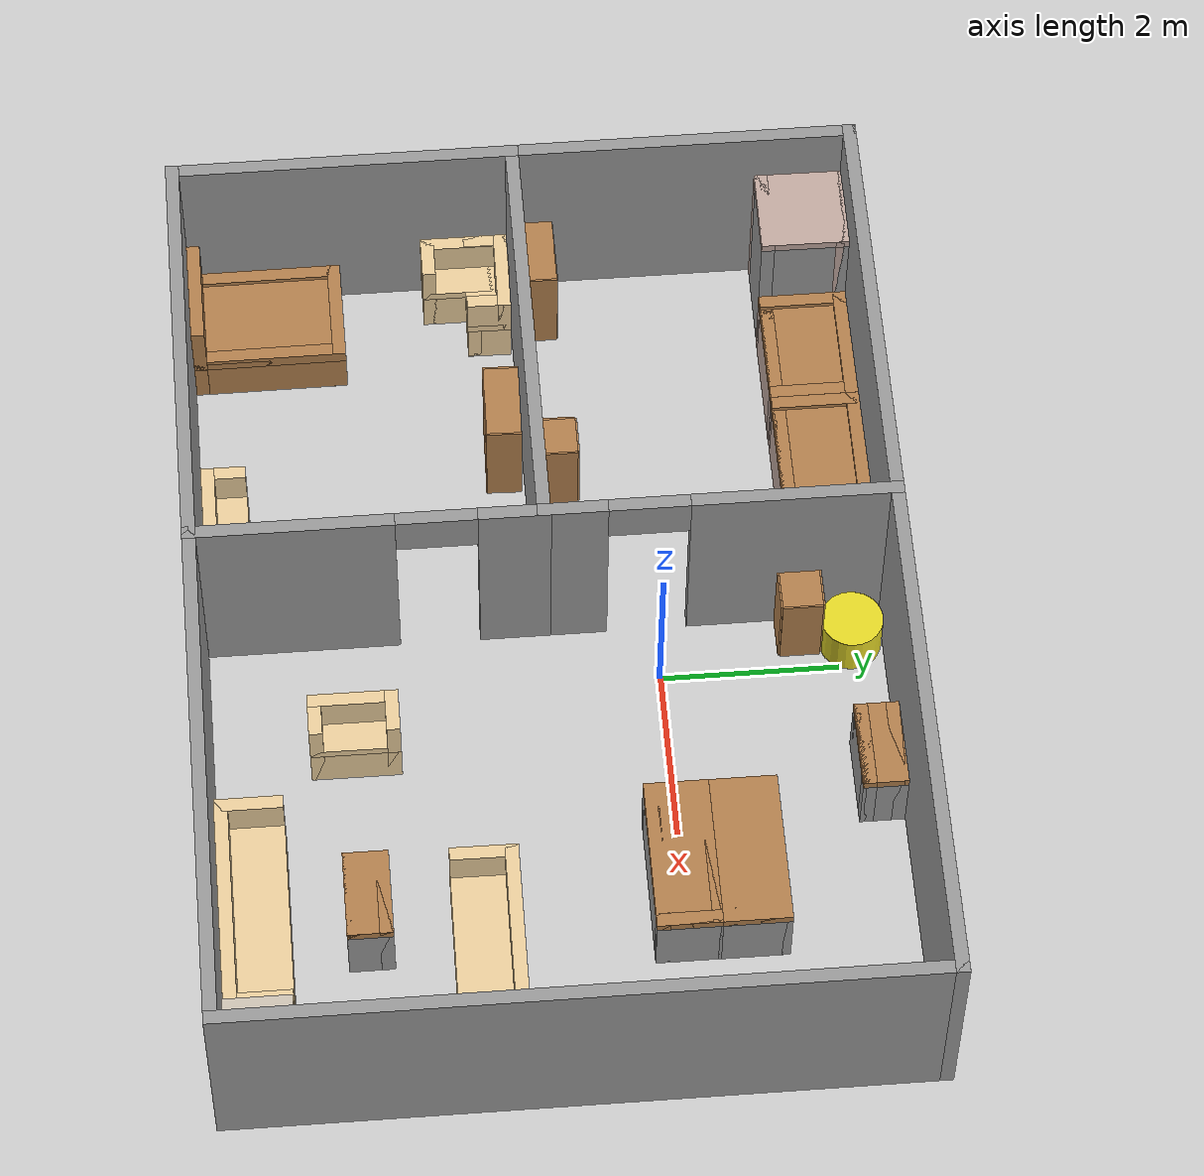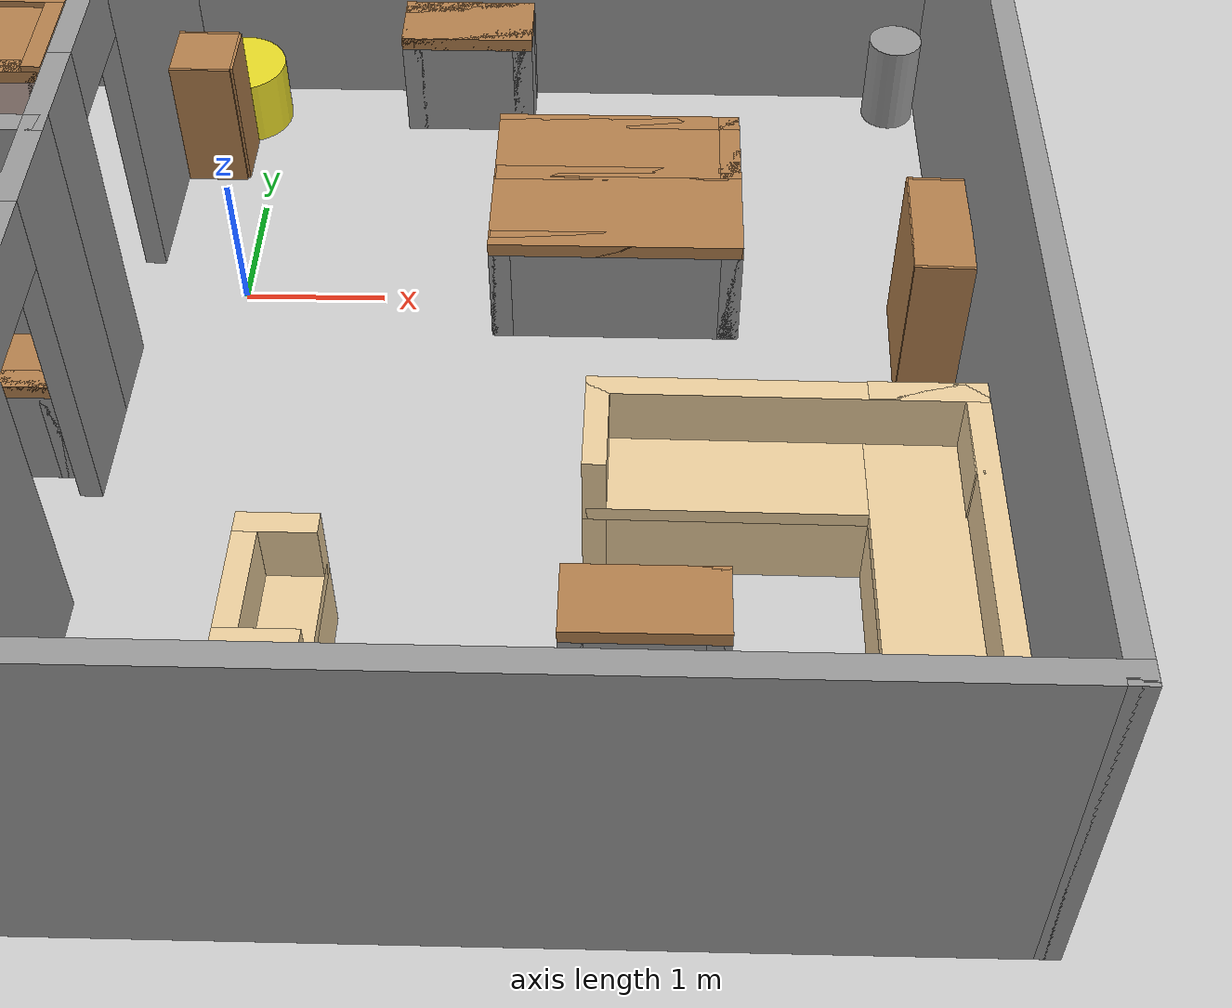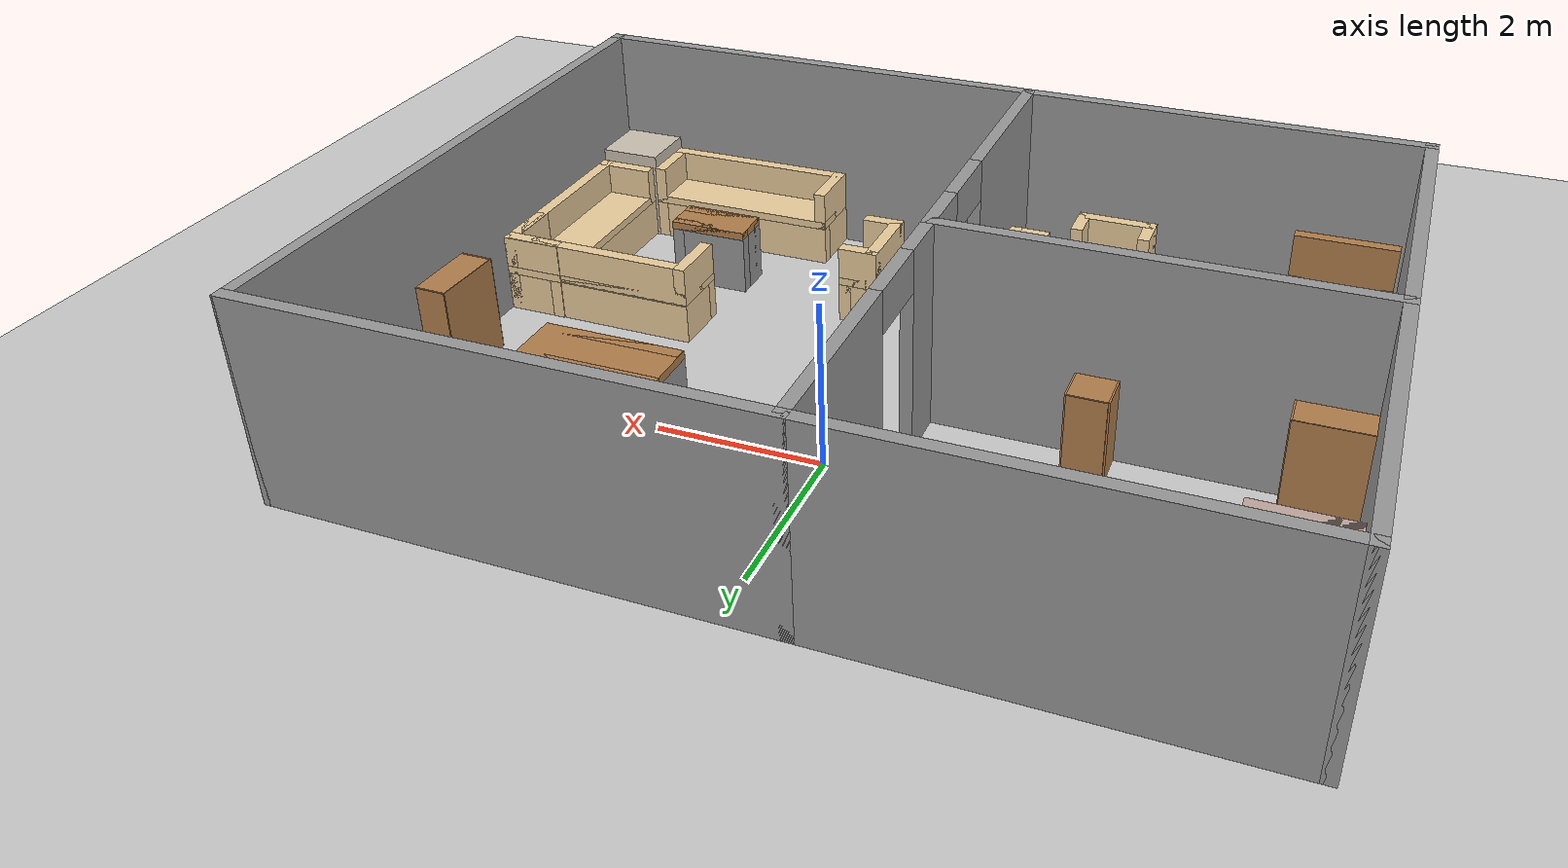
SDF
<sdf version="1.6">
 <world name="default">
  <light name="sun" type="directional">
   <pose>0 0 10 0 -0 0</pose>
   <diffuse>0.8 0.8 0.8 1</diffuse>
   <specular>0.2 0.2 0.2 1</specular>
   <attenuation>
    <range>1000</range>
    <constant>0.9</constant>
    <linear>0.01</linear>
    <quadratic>0.001</quadratic>
   </attenuation>
   <direction>-0.5 0.1 -0.9</direction>
  </light>
  <model name="ground_plane">
   <static>1</static>
   <link name="link">
    <collision name="collision">
     <geometry><plane><normal>0 0 1</normal><size>100 100</size></plane></geometry>
     <surface><friction><ode><mu>100</mu><mu2>50</mu2></ode></friction></surface>
    </collision>
    <visual name="visual">
     <cast_shadows>0</cast_shadows>
     <geometry><plane><normal>0 0 1</normal><size>100 100</size></plane></geometry>
     <material>
      <script><uri>file://media/materials/scripts/gazebo.material</uri><name>Gazebo/Grey</name></script>
     </material>
    </visual>
   </link>
  </model>
  <gravity>0 0 -9.8</gravity>
  <magnetic_field>6e-06 2.3e-05 -4.2e-05</magnetic_field>
  <atmosphere type="adiabatic"/>
  <physics name="default_physics" default="0" type="ode">
   <max_step_size>0.001</max_step_size>
   <real_time_factor>1</real_time_factor>
   <real_time_update_rate>1000</real_time_update_rate>
  </physics>
  <scene><ambient>0.4 0.4 0.4 1</ambient><background>0.7 0.7 0.7 1</background><shadows>1</shadows></scene>
  <spherical_coordinates>
   <surface_model>EARTH_WGS84</surface_model>
   <latitude_deg>0</latitude_deg>
   <longitude_deg>0</longitude_deg>
   <elevation>0</elevation>
   <heading_deg>0</heading_deg>
  </spherical_coordinates>
  <model name="project.world">
   <pose>-0.23315 -1.25474 0 0 -0 0</pose>
   <link name="Wall_16">
    <collision name="Wall_16_Collision">
     <geometry><box><size>5 0.15 2.5</size></box></geometry>
     <pose>0 0 1.25 0 -0 0</pose>
    </collision>
    <visual name="Wall_16_Visual">
     <pose>0 0 1.25 0 -0 0</pose>
     <geometry><box><size>5 0.15 2.5</size></box></geometry>
     <material>
      <script><uri>file://media/materials/scripts/gazebo.material</uri><name>Gazebo/Grey</name></script>
      <ambient>1 1 1 1</ambient>
     </material>
     <meta><layer>0</layer></meta>
    </visual>
    <pose>-2.925 -3.85 0 0 -0 0</pose>
   </link>
   <link name="Wall_18">
    <collision name="Wall_18_Collision">
     <geometry><box><size>4 0.15 2.5</size></box></geometry>
     <pose>0 0 1.25 0 -0 0</pose>
    </collision>
    <visual name="Wall_18_Visual">
     <pose>0 0 1.25 0 -0 0</pose>
     <geometry><box><size>4 0.15 2.5</size></box></geometry>
     <material>
      <script><uri>file://media/materials/scripts/gazebo.material</uri><name>Gazebo/Grey</name></script>
      <ambient>1 1 1 1</ambient>
     </material>
     <meta><layer>0</layer></meta>
    </visual>
    <pose>-5.35 -1.925 0 0 -0 1.5708</pose>
   </link>
   <link name="Wall_19">
    <collision name="Wall_19_Collision">
     <geometry><box><size>4 0.15 2.5</size></box></geometry>
     <pose>0 0 1.25 0 -0 0</pose>
    </collision>
    <visual name="Wall_19_Visual">
     <pose>0 0 1.25 0 -0 0</pose>
     <geometry><box><size>4 0.15 2.5</size></box></geometry>
     <material>
      <script><uri>file://media/materials/scripts/gazebo.material</uri><name>Gazebo/Grey</name></script>
      <ambient>1 1 1 1</ambient>
     </material>
     <meta><layer>0</layer></meta>
    </visual>
    <pose>-5.35 1.925 0 0 -0 1.5708</pose>
   </link>
   <link name="Wall_20">
    <collision name="Wall_20_Collision">
     <geometry><box><size>5 0.15 2.5</size></box></geometry>
     <pose>0 0 1.25 0 -0 0</pose>
    </collision>
    <visual name="Wall_20_Visual">
     <pose>0 0 1.25 0 -0 0</pose>
     <geometry><box><size>5 0.15 2.5</size></box></geometry>
     <material>
      <script><uri>file://media/materials/scripts/gazebo.material</uri><name>Gazebo/Grey</name></script>
      <ambient>1 1 1 1</ambient>
     </material>
     <meta><layer>0</layer></meta>
    </visual>
    <pose>-2.925 3.85 0 0 -0 0</pose>
   </link>
   <link name="Wall_21">
    <pose>-0.5 1.925 0 0 0 -1.5708</pose>
    <visual name="Wall_21_Visual_0">
     <pose>-0.8375 0 1.25 0 -0 0</pose>
     <geometry><box><size>2.325 0.15 2.5</size></box></geometry>
     <material>
      <script><uri>file://media/materials/scripts/gazebo.material</uri><name>Gazebo/Grey</name></script>
      <ambient>1 1 1 1</ambient>
     </material>
     <meta><layer>0</layer></meta>
    </visual>
    <collision name="Wall_21_Collision_0">
     <geometry><box><size>2.325 0.15 2.5</size></box></geometry>
     <pose>-0.8375 0 1.25 0 -0 0</pose>
    </collision>
    <visual name="Wall_21_Visual_1">
     <pose>1.6125 0 1.25 0 -0 0</pose>
     <geometry><box><size>0.775 0.15 2.5</size></box></geometry>
     <material>
      <script><uri>file://media/materials/scripts/gazebo.material</uri><name>Gazebo/Grey</name></script>
      <ambient>1 1 1 1</ambient>
     </material>
     <meta><layer>0</layer></meta>
    </visual>
    <collision name="Wall_21_Collision_1">
     <geometry><box><size>0.775 0.15 2.5</size></box></geometry>
     <pose>1.6125 0 1.25 0 -0 0</pose>
    </collision>
    <visual name="Wall_21_Visual_2">
     <pose>0.775 0 2.25 0 -0 0</pose>
     <geometry><box><size>0.9 0.15 0.5</size></box></geometry>
     <material>
      <script><uri>file://media/materials/scripts/gazebo.material</uri><name>Gazebo/Grey</name></script>
      <ambient>1 1 1 1</ambient>
     </material>
     <meta><layer>0</layer></meta>
    </visual>
    <collision name="Wall_21_Collision_2">
     <geometry><box><size>0.9 0.15 0.5</size></box></geometry>
     <pose>0.775 0 2.25 0 -0 0</pose>
    </collision>
   </link>
   <link name="Wall_22">
    <collision name="Wall_22_Collision">
     <geometry><box><size>5 0.15 2.5</size></box></geometry>
     <pose>0 0 1.25 0 -0 0</pose>
    </collision>
    <visual name="Wall_22_Visual">
     <pose>0 0 1.25 0 -0 0</pose>
     <geometry><box><size>5 0.15 2.5</size></box></geometry>
     <material>
      <script><uri>file://media/materials/scripts/gazebo.material</uri><name>Gazebo/Grey</name></script>
      <ambient>1 1 1 1</ambient>
     </material>
     <meta><layer>0</layer></meta>
    </visual>
    <pose>-2.925 0 0 0 -0 3.14159</pose>
   </link>
   <link name="Wall_25">
    <pose>-0.5 -1.925 0 0 0 -1.5708</pose>
    <visual name="Wall_25_Visual_0">
     <pose>-1.6025 0 1.25 0 -0 0</pose>
     <geometry><box><size>0.795 0.15 2.5</size></box></geometry>
     <material>
      <script><uri>file://media/materials/scripts/gazebo.material</uri><name>Gazebo/Grey</name></script>
      <ambient>1 1 1 1</ambient>
     </material>
     <meta><layer>0</layer></meta>
    </visual>
    <collision name="Wall_25_Collision_0">
     <geometry><box><size>0.795 0.15 2.5</size></box></geometry>
     <pose>-1.6025 0 1.25 0 -0 0</pose>
    </collision>
    <visual name="Wall_25_Visual_1">
     <pose>0.8475 0 1.25 0 -0 0</pose>
     <geometry><box><size>2.305 0.15 2.5</size></box></geometry>
     <material>
      <script><uri>file://media/materials/scripts/gazebo.material</uri><name>Gazebo/Grey</name></script>
      <ambient>1 1 1 1</ambient>
     </material>
     <meta><layer>0</layer></meta>
    </visual>
    <collision name="Wall_25_Collision_1">
     <geometry><box><size>2.305 0.15 2.5</size></box></geometry>
     <pose>0.8475 0 1.25 0 -0 0</pose>
    </collision>
    <visual name="Wall_25_Visual_2">
     <pose>-0.755 0 2.25 0 -0 0</pose>
     <geometry><box><size>0.9 0.15 0.5</size></box></geometry>
     <material>
      <script><uri>file://media/materials/scripts/gazebo.material</uri><name>Gazebo/Grey</name></script>
      <ambient>1 1 1 1</ambient>
     </material>
     <meta><layer>0</layer></meta>
    </visual>
    <collision name="Wall_25_Collision_2">
     <geometry><box><size>0.9 0.15 0.5</size></box></geometry>
     <pose>-0.755 0 2.25 0 -0 0</pose>
    </collision>
   </link>
   <link name="Wall_27">
    <collision name="Wall_27_Collision">
     <geometry><box><size>6 0.15 2.5</size></box></geometry>
     <pose>0 0 1.25 0 -0 0</pose>
    </collision>
    <visual name="Wall_27_Visual">
     <pose>0 0 1.25 0 -0 0</pose>
     <geometry><box><size>6 0.15 2.5</size></box></geometry>
     <material>
      <script><uri>file://media/materials/scripts/gazebo.material</uri><name>Gazebo/Grey</name></script>
      <ambient>1 1 1 1</ambient>
     </material>
     <meta><layer>0</layer></meta>
    </visual>
    <pose>2.425 -3.85 0 0 -0 0</pose>
   </link>
   <link name="Wall_28">
    <collision name="Wall_28_Collision">
     <geometry><box><size>7.85 0.15 2.5</size></box></geometry>
     <pose>0 0 1.25 0 -0 0</pose>
    </collision>
    <visual name="Wall_28_Visual">
     <pose>0 0 1.25 0 -0 0</pose>
     <geometry><box><size>7.85 0.15 2.5</size></box></geometry>
     <material>
      <script><uri>file://media/materials/scripts/gazebo.material</uri><name>Gazebo/Grey</name></script>
      <ambient>1 1 1 1</ambient>
     </material>
     <meta><layer>0</layer></meta>
    </visual>
    <pose>5.35 0 0 0 -0 1.5708</pose>
   </link>
   <link name="Wall_30">
    <collision name="Wall_30_Collision">
     <geometry><box><size>6 0.15 2.5</size></box></geometry>
     <pose>0 0 1.25 0 -0 0</pose>
    </collision>
    <visual name="Wall_30_Visual">
     <pose>0 0 1.25 0 -0 0</pose>
     <geometry><box><size>6 0.15 2.5</size></box></geometry>
     <material>
      <script><uri>file://media/materials/scripts/gazebo.material</uri><name>Gazebo/Grey</name></script>
      <ambient>1 1 1 1</ambient>
     </material>
     <meta><layer>0</layer></meta>
    </visual>
    <pose>2.425 3.85 0 0 -0 0</pose>
   </link>
   <static>1</static>
  </model>
  <model name="sofa_long.world">
   <pose>2.99095 -4.64793 0 0 -0 0</pose>
   <link name="Floor_1">
    <collision name="Floor_1_Collision">
     <geometry><box><size>2.5 0.75 0.1</size></box></geometry>
     <pose>0 0 0.05 0 -0 0</pose>
    </collision>
    <visual name="Floor_1_Visual">
     <pose>0 0 0.05 0 -0 0</pose>
     <geometry><box><size>2.5 0.75 0.1</size></box></geometry>
     <material>
      <script><uri>file://media/materials/scripts/gazebo.material</uri><name>Gazebo/Grey</name></script>
      <ambient>0.921569 0.807843 0.615686 1</ambient>
     </material>
     <meta><layer>1</layer></meta>
    </visual>
    <pose>0 0 0.5 0 -0 0</pose>
   </link>
   <link name="Wall_11">
    <collision name="Wall_11_Collision">
     <geometry><box><size>2.5 0.15 0.5</size></box></geometry>
     <pose>0 0 0.25 0 -0 0</pose>
    </collision>
    <visual name="Wall_11_Visual">
     <pose>0 0 0.25 0 -0 0</pose>
     <geometry><box><size>2.5 0.15 0.5</size></box></geometry>
     <material>
      <script><uri>file://media/materials/scripts/gazebo.material</uri><name>Gazebo/Grey</name></script>
      <ambient>0.921569 0.807843 0.615686 1</ambient>
     </material>
     <meta><layer>0</layer></meta>
    </visual>
    <pose>0 -0.3 0 0 -0 0</pose>
   </link>
   <link name="Wall_12">
    <collision name="Wall_12_Collision">
     <geometry><box><size>0.75 0.15 0.5</size></box></geometry>
     <pose>0 0 0.25 0 -0 0</pose>
    </collision>
    <visual name="Wall_12_Visual">
     <pose>0 0 0.25 0 -0 0</pose>
     <geometry><box><size>0.75 0.15 0.5</size></box></geometry>
     <material>
      <script><uri>file://media/materials/scripts/gazebo.material</uri><name>Gazebo/Grey</name></script>
      <ambient>0.921569 0.807843 0.615686 1</ambient>
     </material>
     <meta><layer>0</layer></meta>
    </visual>
    <pose>1.175 0 0 0 -0 1.5708</pose>
   </link>
   <link name="Wall_13">
    <collision name="Wall_13_Collision">
     <geometry><box><size>2.5 0.15 0.5</size></box></geometry>
     <pose>0 0 0.25 0 -0 0</pose>
    </collision>
    <visual name="Wall_13_Visual">
     <pose>0 0 0.25 0 -0 0</pose>
     <geometry><box><size>2.5 0.15 0.5</size></box></geometry>
     <material>
      <script><uri>file://media/materials/scripts/gazebo.material</uri><name>Gazebo/Grey</name></script>
      <ambient>0.921569 0.807843 0.615686 1</ambient>
     </material>
     <meta><layer>0</layer></meta>
    </visual>
    <pose>0 0.3 0 0 -0 3.14159</pose>
   </link>
   <link name="Wall_14">
    <collision name="Wall_14_Collision">
     <geometry><box><size>0.75 0.15 0.5</size></box></geometry>
     <pose>0 0 0.25 0 -0 0</pose>
    </collision>
    <visual name="Wall_14_Visual">
     <pose>0 0 0.25 0 -0 0</pose>
     <geometry><box><size>0.75 0.15 0.5</size></box></geometry>
     <material>
      <script><uri>file://media/materials/scripts/gazebo.material</uri><name>Gazebo/Grey</name></script>
      <ambient>0.921569 0.807843 0.615686 1</ambient>
     </material>
     <meta><layer>0</layer></meta>
    </visual>
    <pose>-1.175 0 0 0 0 -1.5708</pose>
   </link>
   <link name="Wall_16">
    <collision name="Wall_16_Collision">
     <geometry><box><size>2.5 0.15 0.5</size></box></geometry>
     <pose>0 0 0.25 0 -0 0</pose>
    </collision>
    <visual name="Wall_16_Visual">
     <pose>0 0 0.25 0 -0 0</pose>
     <geometry><box><size>2.5 0.15 0.5</size></box></geometry>
     <material>
      <script><uri>file://media/materials/scripts/gazebo.material</uri><name>Gazebo/Grey</name></script>
      <ambient>0.921569 0.807843 0.615686 1</ambient>
     </material>
     <meta><layer>1</layer></meta>
    </visual>
    <pose>0 -0.3 0.5 0 -0 0</pose>
   </link>
   <link name="Wall_17">
    <collision name="Wall_17_Collision">
     <geometry><box><size>0.75 0.15 0.5</size></box></geometry>
     <pose>0 0 0.25 0 -0 0</pose>
    </collision>
    <visual name="Wall_17_Visual">
     <pose>0 0 0.25 0 -0 0</pose>
     <geometry><box><size>0.75 0.15 0.5</size></box></geometry>
     <material>
      <script><uri>file://media/materials/scripts/gazebo.material</uri><name>Gazebo/Grey</name></script>
      <ambient>0.921569 0.807843 0.615686 1</ambient>
     </material>
     <meta><layer>1</layer></meta>
    </visual>
    <pose>1.175 0 0.5 0 -0 1.5708</pose>
   </link>
   <link name="Wall_19">
    <collision name="Wall_19_Collision">
     <geometry><box><size>0.75 0.15 0.5</size></box></geometry>
     <pose>0 0 0.25 0 -0 0</pose>
    </collision>
    <visual name="Wall_19_Visual">
     <pose>0 0 0.25 0 -0 0</pose>
     <geometry><box><size>0.75 0.15 0.5</size></box></geometry>
     <material>
      <script><uri>file://media/materials/scripts/gazebo.material</uri><name>Gazebo/Grey</name></script>
      <ambient>0.921569 0.807843 0.615686 1</ambient>
     </material>
     <meta><layer>1</layer></meta>
    </visual>
    <pose>-1.175 0 0.5 0 0 -1.5708</pose>
   </link>
   <static>1</static>
  </model>
  <model name="sofa_long.world_0">
   <pose>4.65758 -3.03297 0 0 -0 1.56969</pose>
   <link name="Floor_1">
    <collision name="Floor_1_Collision">
     <geometry><box><size>2.5 0.75 0.1</size></box></geometry>
     <pose>0 0 0.05 0 -0 0</pose>
    </collision>
    <visual name="Floor_1_Visual">
     <pose>0 0 0.05 0 -0 0</pose>
     <geometry><box><size>2.5 0.75 0.1</size></box></geometry>
     <material>
      <script><uri>file://media/materials/scripts/gazebo.material</uri><name>Gazebo/Grey</name></script>
      <ambient>0.921569 0.807843 0.615686 1</ambient>
     </material>
     <meta><layer>1</layer></meta>
    </visual>
    <pose>0 0 0.5 0 -0 0</pose>
   </link>
   <link name="Wall_11">
    <collision name="Wall_11_Collision">
     <geometry><box><size>2.5 0.15 0.5</size></box></geometry>
     <pose>0 0 0.25 0 -0 0</pose>
    </collision>
    <visual name="Wall_11_Visual">
     <pose>0 0 0.25 0 -0 0</pose>
     <geometry><box><size>2.5 0.15 0.5</size></box></geometry>
     <material>
      <script><uri>file://media/materials/scripts/gazebo.material</uri><name>Gazebo/Grey</name></script>
      <ambient>0.921569 0.807843 0.615686 1</ambient>
     </material>
     <meta><layer>0</layer></meta>
    </visual>
    <pose>0 -0.3 0 0 -0 0</pose>
   </link>
   <link name="Wall_12">
    <collision name="Wall_12_Collision">
     <geometry><box><size>0.75 0.15 0.5</size></box></geometry>
     <pose>0 0 0.25 0 -0 0</pose>
    </collision>
    <visual name="Wall_12_Visual">
     <pose>0 0 0.25 0 -0 0</pose>
     <geometry><box><size>0.75 0.15 0.5</size></box></geometry>
     <material>
      <script><uri>file://media/materials/scripts/gazebo.material</uri><name>Gazebo/Grey</name></script>
      <ambient>0.921569 0.807843 0.615686 1</ambient>
     </material>
     <meta><layer>0</layer></meta>
    </visual>
    <pose>1.175 0 0 0 -0 1.5708</pose>
   </link>
   <link name="Wall_13">
    <collision name="Wall_13_Collision">
     <geometry><box><size>2.5 0.15 0.5</size></box></geometry>
     <pose>0 0 0.25 0 -0 0</pose>
    </collision>
    <visual name="Wall_13_Visual">
     <pose>0 0 0.25 0 -0 0</pose>
     <geometry><box><size>2.5 0.15 0.5</size></box></geometry>
     <material>
      <script><uri>file://media/materials/scripts/gazebo.material</uri><name>Gazebo/Grey</name></script>
      <ambient>0.921569 0.807843 0.615686 1</ambient>
     </material>
     <meta><layer>0</layer></meta>
    </visual>
    <pose>0 0.3 0 0 -0 3.14159</pose>
   </link>
   <link name="Wall_14">
    <collision name="Wall_14_Collision">
     <geometry><box><size>0.75 0.15 0.5</size></box></geometry>
     <pose>0 0 0.25 0 -0 0</pose>
    </collision>
    <visual name="Wall_14_Visual">
     <pose>0 0 0.25 0 -0 0</pose>
     <geometry><box><size>0.75 0.15 0.5</size></box></geometry>
     <material>
      <script><uri>file://media/materials/scripts/gazebo.material</uri><name>Gazebo/Grey</name></script>
      <ambient>0.921569 0.807843 0.615686 1</ambient>
     </material>
     <meta><layer>0</layer></meta>
    </visual>
    <pose>-1.175 0 0 0 0 -1.5708</pose>
   </link>
   <link name="Wall_16">
    <collision name="Wall_16_Collision">
     <geometry><box><size>2.5 0.15 0.5</size></box></geometry>
     <pose>0 0 0.25 0 -0 0</pose>
    </collision>
    <visual name="Wall_16_Visual">
     <pose>0 0 0.25 0 -0 0</pose>
     <geometry><box><size>2.5 0.15 0.5</size></box></geometry>
     <material>
      <script><uri>file://media/materials/scripts/gazebo.material</uri><name>Gazebo/Grey</name></script>
      <ambient>0.921569 0.807843 0.615686 1</ambient>
     </material>
     <meta><layer>1</layer></meta>
    </visual>
    <pose>0 -0.3 0.5 0 -0 0</pose>
   </link>
   <link name="Wall_17">
    <collision name="Wall_17_Collision">
     <geometry><box><size>0.75 0.15 0.5</size></box></geometry>
     <pose>0 0 0.25 0 -0 0</pose>
    </collision>
    <visual name="Wall_17_Visual">
     <pose>0 0 0.25 0 -0 0</pose>
     <geometry><box><size>0.75 0.15 0.5</size></box></geometry>
     <material>
      <script><uri>file://media/materials/scripts/gazebo.material</uri><name>Gazebo/Grey</name></script>
      <ambient>0.921569 0.807843 0.615686 1</ambient>
     </material>
     <meta><layer>1</layer></meta>
    </visual>
    <pose>1.175 0 0.5 0 -0 1.5708</pose>
   </link>
   <link name="Wall_19">
    <collision name="Wall_19_Collision">
     <geometry><box><size>0.75 0.15 0.5</size></box></geometry>
     <pose>0 0 0.25 0 -0 0</pose>
    </collision>
    <visual name="Wall_19_Visual">
     <pose>0 0 0.25 0 -0 0</pose>
     <geometry><box><size>0.75 0.15 0.5</size></box></geometry>
     <material>
      <script><uri>file://media/materials/scripts/gazebo.material</uri><name>Gazebo/Grey</name></script>
      <ambient>0.921569 0.807843 0.615686 1</ambient>
     </material>
     <meta><layer>1</layer></meta>
    </visual>
    <pose>-1.175 0 0.5 0 0 -1.5708</pose>
   </link>
   <static>1</static>
  </model>
  <model name="table_small.world">
   <pose>2.91825 -3.42446 0 0 -0 0</pose>
   <link name="Floor_2">
    <collision name="Floor_2_Collision">
     <geometry><box><size>1 0.5 0.1</size></box></geometry>
     <pose>0 0 0.05 0 -0 0</pose>
    </collision>
    <visual name="Floor_2_Visual">
     <pose>0 0 0.05 0 -0 0</pose>
     <geometry><box><size>1 0.5 0.1</size></box></geometry>
     <material>
      <script><uri>file://media/materials/scripts/gazebo.material</uri><name>Gazebo/Wood</name></script>
      <ambient>1 1 1 1</ambient>
     </material>
     <meta><layer>1</layer></meta>
    </visual>
    <pose>0 0 0.75 0 -0 0</pose>
   </link>
   <link name="Wall_10">
    <collision name="Wall_10_Collision">
     <geometry><box><size>0.5 0.15 0.75</size></box></geometry>
     <pose>0 0 0.375 0 -0 0</pose>
    </collision>
    <visual name="Wall_10_Visual">
     <pose>0 0 0.375 0 -0 0</pose>
     <geometry><box><size>0.5 0.15 0.75</size></box></geometry>
     <material>
      <script><uri>file://media/materials/scripts/gazebo.material</uri><name>Gazebo/Grey</name></script>
      <ambient>1 1 1 1</ambient>
     </material>
     <meta><layer>0</layer></meta>
    </visual>
    <pose>0.425 0 0 0 -0 1.5708</pose>
   </link>
   <link name="Wall_11">
    <collision name="Wall_11_Collision">
     <geometry><box><size>1 0.15 0.75</size></box></geometry>
     <pose>0 0 0.375 0 -0 0</pose>
    </collision>
    <visual name="Wall_11_Visual">
     <pose>0 0 0.375 0 -0 0</pose>
     <geometry><box><size>1 0.15 0.75</size></box></geometry>
     <material>
      <script><uri>file://media/materials/scripts/gazebo.material</uri><name>Gazebo/Grey</name></script>
      <ambient>1 1 1 1</ambient>
     </material>
     <meta><layer>0</layer></meta>
    </visual>
    <pose>0 0.175 0 0 -0 3.14159</pose>
   </link>
   <link name="Wall_12">
    <collision name="Wall_12_Collision">
     <geometry><box><size>0.5 0.15 0.75</size></box></geometry>
     <pose>0 0 0.375 0 -0 0</pose>
    </collision>
    <visual name="Wall_12_Visual">
     <pose>0 0 0.375 0 -0 0</pose>
     <geometry><box><size>0.5 0.15 0.75</size></box></geometry>
     <material>
      <script><uri>file://media/materials/scripts/gazebo.material</uri><name>Gazebo/Grey</name></script>
      <ambient>1 1 1 1</ambient>
     </material>
     <meta><layer>0</layer></meta>
    </visual>
    <pose>-0.425 0 0 0 0 -1.5708</pose>
   </link>
   <link name="Wall_19">
    <collision name="Wall_19_Collision">
     <geometry><box><size>1 0.15 0.1</size></box></geometry>
     <pose>0 0 0.05 0 -0 0</pose>
    </collision>
    <visual name="Wall_19_Visual">
     <pose>0 0 0.05 0 -0 0</pose>
     <geometry><box><size>1 0.15 0.1</size></box></geometry>
     <material>
      <script><uri>file://media/materials/scripts/gazebo.material</uri><name>Gazebo/Wood</name></script>
      <ambient>1 1 1 1</ambient>
     </material>
     <meta><layer>1</layer></meta>
    </visual>
    <pose>0 -0.175 0.75 0 -0 0</pose>
   </link>
   <link name="Wall_21">
    <collision name="Wall_21_Collision">
     <geometry><box><size>1 0.15 0.1</size></box></geometry>
     <pose>0 0 0.05 0 -0 0</pose>
    </collision>
    <visual name="Wall_21_Visual">
     <pose>0 0 0.05 0 -0 0</pose>
     <geometry><box><size>1 0.15 0.1</size></box></geometry>
     <material>
      <script><uri>file://media/materials/scripts/gazebo.material</uri><name>Gazebo/Wood</name></script>
      <ambient>1 1 1 1</ambient>
     </material>
     <meta><layer>1</layer></meta>
    </visual>
    <pose>0 0.175 0.75 0 -0 3.14159</pose>
   </link>
   <link name="Wall_9">
    <collision name="Wall_9_Collision">
     <geometry><box><size>1 0.15 0.75</size></box></geometry>
     <pose>0 0 0.375 0 -0 0</pose>
    </collision>
    <visual name="Wall_9_Visual">
     <pose>0 0 0.375 0 -0 0</pose>
     <geometry><box><size>1 0.15 0.75</size></box></geometry>
     <material>
      <script><uri>file://media/materials/scripts/gazebo.material</uri><name>Gazebo/Grey</name></script>
      <ambient>1 1 1 1</ambient>
     </material>
     <meta><layer>0</layer></meta>
    </visual>
    <pose>0 -0.175 0 0 -0 0</pose>
   </link>
   <static>1</static>
  </model>
  <model name="bookshelf">
   <static>1</static>
   <link name="link">
    <inertial><mass>1</mass></inertial>
    <collision name="back">
     <pose>0 0.005 0.6 0 -0 0</pose>
     <geometry><box><size>0.9 0.01 1.2</size></box></geometry>
    </collision>
    <visual name="visual1">
     <pose>0 0.005 0.6 0 -0 0</pose>
     <geometry><box><size>0.9 0.01 1.2</size></box></geometry>
     <material>
      <script><uri>file://media/materials/scripts/gazebo.material</uri><name>Gazebo/Wood</name></script>
     </material>
    </visual>
    <collision name="left_side">
     <pose>0.45 -0.195 0.6 0 -0 0</pose>
     <geometry><box><size>0.02 0.4 1.2</size></box></geometry>
    </collision>
    <visual name="visual2">
     <pose>0.45 -0.195 0.6 0 -0 0</pose>
     <geometry><box><size>0.02 0.4 1.2</size></box></geometry>
     <material>
      <script><uri>file://media/materials/scripts/gazebo.material</uri><name>Gazebo/Wood</name></script>
     </material>
    </visual>
    <collision name="right_side">
     <pose>-0.45 -0.195 0.6 0 -0 0</pose>
     <geometry><box><size>0.02 0.4 1.2</size></box></geometry>
    </collision>
    <visual name="visual3">
     <pose>-0.45 -0.195 0.6 0 -0 0</pose>
     <geometry><box><size>0.02 0.4 1.2</size></box></geometry>
     <material>
      <script><uri>file://media/materials/scripts/gazebo.material</uri><name>Gazebo/Wood</name></script>
     </material>
    </visual>
    <collision name="bottom">
     <pose>0 -0.195 0.03 0 -0 0</pose>
     <geometry><box><size>0.88 0.4 0.06</size></box></geometry>
    </collision>
    <visual name="visual4">
     <pose>0 -0.195 0.03 0 -0 0</pose>
     <geometry><box><size>0.88 0.4 0.06</size></box></geometry>
     <material>
      <script><uri>file://media/materials/scripts/gazebo.material</uri><name>Gazebo/Wood</name></script>
     </material>
    </visual>
    <collision name="top">
     <pose>0 -0.195 1.19 0 -0 0</pose>
     <geometry><box><size>0.88 0.4 0.02</size></box></geometry>
    </collision>
    <visual name="visual5">
     <pose>0 -0.195 1.19 0 -0 0</pose>
     <geometry><box><size>0.88 0.4 0.02</size></box></geometry>
     <material>
      <script><uri>file://media/materials/scripts/gazebo.material</uri><name>Gazebo/Wood</name></script>
     </material>
    </visual>
    <collision name="low_shelf">
     <pose>0 -0.195 0.43 0 -0 0</pose>
     <geometry><box><size>0.88 0.4 0.02</size></box></geometry>
    </collision>
    <visual name="visual6">
     <pose>0 -0.195 0.43 0 -0 0</pose>
     <geometry><box><size>0.88 0.4 0.02</size></box></geometry>
     <material>
      <script><uri>file://media/materials/scripts/gazebo.material</uri><name>Gazebo/Wood</name></script>
     </material>
    </visual>
    <collision name="high_shelf">
     <pose>0 -0.195 0.8 0 -0 0</pose>
     <geometry><box><size>0.88 0.4 0.02</size></box></geometry>
    </collision>
    <visual name="visual7">
     <pose>0 -0.195 0.8 0 -0 0</pose>
     <geometry><box><size>0.88 0.4 0.02</size></box></geometry>
     <material>
      <script><uri>file://media/materials/scripts/gazebo.material</uri><name>Gazebo/Wood</name></script>
     </material>
    </visual>
   </link>
   <pose>4.64829 -0.47118 0 0 -0 1.5424</pose>
  </model>
  <model name="table_big_.world">
   <pose>2.68876 0.715463 0 0 -0 0</pose>
   <link name="Floor_0">
    <collision name="Floor_0_Collision">
     <geometry><box><size>1.75 0.75 0.1</size></box></geometry>
     <pose>0 0 0.05 0 -0 0</pose>
    </collision>
    <visual name="Floor_0_Visual">
     <pose>0 0 0.05 0 -0 0</pose>
     <geometry><box><size>1.75 0.75 0.1</size></box></geometry>
     <material>
      <script><uri>file://media/materials/scripts/gazebo.material</uri><name>Gazebo/Wood</name></script>
      <ambient>1 1 1 1</ambient>
     </material>
     <meta><layer>1</layer></meta>
    </visual>
    <pose>0 0 0.75 0 -0 0</pose>
   </link>
   <link name="Wall_1">
    <collision name="Wall_1_Collision">
     <geometry><box><size>0.75 0.15 0.75</size></box></geometry>
     <pose>0 0 0.375 0 -0 0</pose>
    </collision>
    <visual name="Wall_1_Visual">
     <pose>0 0 0.375 0 -0 0</pose>
     <geometry><box><size>0.75 0.15 0.75</size></box></geometry>
     <material>
      <script><uri>file://media/materials/scripts/gazebo.material</uri><name>Gazebo/Grey</name></script>
      <ambient>1 1 1 1</ambient>
     </material>
     <meta><layer>0</layer></meta>
    </visual>
    <pose>0.8 0 0 0 -0 1.5708</pose>
   </link>
   <link name="Wall_11">
    <collision name="Wall_11_Collision">
     <geometry><box><size>1.73 0.15 0.1</size></box></geometry>
     <pose>0 0 0.05 0 -0 0</pose>
    </collision>
    <visual name="Wall_11_Visual">
     <pose>0 0 0.05 0 -0 0</pose>
     <geometry><box><size>1.73 0.15 0.1</size></box></geometry>
     <material>
      <script><uri>file://media/materials/scripts/gazebo.material</uri><name>Gazebo/Wood</name></script>
      <ambient>1 1 1 1</ambient>
     </material>
     <meta><layer>1</layer></meta>
    </visual>
    <pose>0 -0.3 0.75 0 -0 3.14159</pose>
   </link>
   <link name="Wall_12">
    <collision name="Wall_12_Collision">
     <geometry><box><size>0.75 0.15 0.1</size></box></geometry>
     <pose>0 0 0.05 0 -0 0</pose>
    </collision>
    <visual name="Wall_12_Visual">
     <pose>0 0 0.05 0 -0 0</pose>
     <geometry><box><size>0.75 0.15 0.1</size></box></geometry>
     <material>
      <script><uri>file://media/materials/scripts/gazebo.material</uri><name>Gazebo/Wood</name></script>
      <ambient>1 1 1 1</ambient>
     </material>
     <meta><layer>1</layer></meta>
    </visual>
    <pose>0.8 0 0.75 0 0 -1.5708</pose>
   </link>
   <link name="Wall_13">
    <collision name="Wall_13_Collision">
     <geometry><box><size>0.16 0.15 0.1</size></box></geometry>
     <pose>0 0 0.05 0 -0 0</pose>
    </collision>
    <visual name="Wall_13_Visual">
     <pose>0 0 0.05 0 -0 0</pose>
     <geometry><box><size>0.16 0.15 0.1</size></box></geometry>
     <material>
      <script><uri>file://media/materials/scripts/gazebo.material</uri><name>Gazebo/Wood</name></script>
      <ambient>1 1 1 1</ambient>
     </material>
     <meta><layer>1</layer></meta>
    </visual>
    <pose>0.795 -0.3 0.75 0 -0 3.14159</pose>
   </link>
   <link name="Wall_3">
    <collision name="Wall_3_Collision">
     <geometry><box><size>1.75 0.15 0.75</size></box></geometry>
     <pose>0 0 0.375 0 -0 0</pose>
    </collision>
    <visual name="Wall_3_Visual">
     <pose>0 0 0.375 0 -0 0</pose>
     <geometry><box><size>1.75 0.15 0.75</size></box></geometry>
     <material>
      <script><uri>file://media/materials/scripts/gazebo.material</uri><name>Gazebo/Grey</name></script>
      <ambient>1 1 1 1</ambient>
     </material>
     <meta><layer>0</layer></meta>
    </visual>
    <pose>0 0.3 0 0 -0 3.14159</pose>
   </link>
   <link name="Wall_4">
    <collision name="Wall_4_Collision">
     <geometry><box><size>0.75 0.15 0.75</size></box></geometry>
     <pose>0 0 0.375 0 -0 0</pose>
    </collision>
    <visual name="Wall_4_Visual">
     <pose>0 0 0.375 0 -0 0</pose>
     <geometry><box><size>0.75 0.15 0.75</size></box></geometry>
     <material>
      <script><uri>file://media/materials/scripts/gazebo.material</uri><name>Gazebo/Grey</name></script>
      <ambient>1 1 1 1</ambient>
     </material>
     <meta><layer>0</layer></meta>
    </visual>
    <pose>-0.8 0 0 0 0 -1.5708</pose>
   </link>
   <link name="Wall_6">
    <collision name="Wall_6_Collision">
     <geometry><box><size>1.75 0.15 0.75</size></box></geometry>
     <pose>0 0 0.375 0 -0 0</pose>
    </collision>
    <visual name="Wall_6_Visual">
     <pose>0 0 0.375 0 -0 0</pose>
     <geometry><box><size>1.75 0.15 0.75</size></box></geometry>
     <material>
      <script><uri>file://media/materials/scripts/gazebo.material</uri><name>Gazebo/Grey</name></script>
      <ambient>1 1 1 1</ambient>
     </material>
     <meta><layer>0</layer></meta>
    </visual>
    <pose>0 -0.3 0 0 -0 0</pose>
   </link>
   <link name="Wall_9">
    <collision name="Wall_9_Collision">
     <geometry><box><size>1.75 0.15 0.1</size></box></geometry>
     <pose>0 0 0.05 0 -0 0</pose>
    </collision>
    <visual name="Wall_9_Visual">
     <pose>0 0 0.05 0 -0 0</pose>
     <geometry><box><size>1.75 0.15 0.1</size></box></geometry>
     <material>
      <script><uri>file://media/materials/scripts/gazebo.material</uri><name>Gazebo/Wood</name></script>
      <ambient>1 1 1 1</ambient>
     </material>
     <meta><layer>1</layer></meta>
    </visual>
    <pose>0 0.3 0.75 0 -0 3.14159</pose>
   </link>
   <static>1</static>
  </model>
  <model name="livingroom_small_table">
   <link name="link">
    <pose>0 -0.143425 0 0 -0 0</pose>
    <inertial>
     <mass>0.769276</mass>
     <inertia>
      <ixx>0.146265</ixx>
      <ixy>0</ixy>
      <ixz>0</ixz>
      <iyy>0.149979</iyy>
      <iyz>0</iyz>
      <izz>0.0752102</izz>
     </inertia>
    </inertial>
    <visual name="visual">
     <geometry><box><size>0.784585 0.746751 1.313</size></box></geometry>
     <material>
      <script><name>Gazebo/Grey</name><uri>file://media/materials/scripts/gazebo.material</uri></script>
      <shader type="pixel"><normal_map>__default__</normal_map></shader>
      <ambient>0.8 0.76 0.7 1</ambient>
      <diffuse>0.7 0.7 0.7 1</diffuse>
      <specular>0.01 0.01 0.01 1</specular>
      <emissive>0 0 0 1</emissive>
     </material>
    </visual>
    <collision name="collision">
     <geometry><box><size>0.784585 0.746751 1.313</size></box></geometry>
     <surface>
      <friction>
       <ode><mu>1</mu><mu2>1</mu2><fdir1>0 0 0</fdir1><slip1>0</slip1><slip2>0</slip2></ode>
       <torsional>
        <coefficient>1</coefficient>
        <patch_radius>0</patch_radius>
        <surface_radius>0</surface_radius>
        <use_patch_radius>1</use_patch_radius>
        <ode><slip>0</slip></ode>
       </torsional>
      </friction>
      <bounce><restitution_coefficient>0</restitution_coefficient><threshold>1e+06</threshold></bounce>
      <contact>
       <collide_without_contact>0</collide_without_contact>
       <collide_without_contact_bitmask>1</collide_without_contact_bitmask>
       <collide_bitmask>1</collide_bitmask>
       <ode>
        <soft_cfm>0</soft_cfm>
        <soft_erp>0.2</soft_erp>
        <kp>1e+13</kp>
        <kd>1</kd>
        <max_vel>0.01</max_vel>
        <min_depth>0</min_depth>
       </ode>
       <bullet>
        <split_impulse>1</split_impulse>
        <split_impulse_penetration_threshold>-0.01</split_impulse_penetration_threshold>
        <soft_cfm>0</soft_cfm>
        <soft_erp>0.2</soft_erp>
        <kp>1e+13</kp>
        <kd>1</kd>
       </bullet>
      </contact>
     </surface>
    </collision>
   </link>
   <static>1</static>
   <pose>4.62378 -4.51183 0.5 0 -0 0</pose>
  </model>
  <model name="sofa_long.world_1">
   <pose>3.77732 -2.16265 0 0 -0 3.13345</pose>
   <link name="Floor_1">
    <collision name="Floor_1_Collision">
     <geometry><box><size>2.5 0.75 0.1</size></box></geometry>
     <pose>0 0 0.05 0 -0 0</pose>
    </collision>
    <visual name="Floor_1_Visual">
     <pose>0 0 0.05 0 -0 0</pose>
     <geometry><box><size>2.5 0.75 0.1</size></box></geometry>
     <material>
      <script><uri>file://media/materials/scripts/gazebo.material</uri><name>Gazebo/Grey</name></script>
      <ambient>0.921569 0.807843 0.615686 1</ambient>
     </material>
     <meta><layer>1</layer></meta>
    </visual>
    <pose>0 0 0.5 0 -0 0</pose>
   </link>
   <link name="Wall_11">
    <collision name="Wall_11_Collision">
     <geometry><box><size>2.5 0.15 0.5</size></box></geometry>
     <pose>0 0 0.25 0 -0 0</pose>
    </collision>
    <visual name="Wall_11_Visual">
     <pose>0 0 0.25 0 -0 0</pose>
     <geometry><box><size>2.5 0.15 0.5</size></box></geometry>
     <material>
      <script><uri>file://media/materials/scripts/gazebo.material</uri><name>Gazebo/Grey</name></script>
      <ambient>0.921569 0.807843 0.615686 1</ambient>
     </material>
     <meta><layer>0</layer></meta>
    </visual>
    <pose>0 -0.3 0 0 -0 0</pose>
   </link>
   <link name="Wall_12">
    <collision name="Wall_12_Collision">
     <geometry><box><size>0.75 0.15 0.5</size></box></geometry>
     <pose>0 0 0.25 0 -0 0</pose>
    </collision>
    <visual name="Wall_12_Visual">
     <pose>0 0 0.25 0 -0 0</pose>
     <geometry><box><size>0.75 0.15 0.5</size></box></geometry>
     <material>
      <script><uri>file://media/materials/scripts/gazebo.material</uri><name>Gazebo/Grey</name></script>
      <ambient>0.921569 0.807843 0.615686 1</ambient>
     </material>
     <meta><layer>0</layer></meta>
    </visual>
    <pose>1.175 0 0 0 -0 1.5708</pose>
   </link>
   <link name="Wall_13">
    <collision name="Wall_13_Collision">
     <geometry><box><size>2.5 0.15 0.5</size></box></geometry>
     <pose>0 0 0.25 0 -0 0</pose>
    </collision>
    <visual name="Wall_13_Visual">
     <pose>0 0 0.25 0 -0 0</pose>
     <geometry><box><size>2.5 0.15 0.5</size></box></geometry>
     <material>
      <script><uri>file://media/materials/scripts/gazebo.material</uri><name>Gazebo/Grey</name></script>
      <ambient>0.921569 0.807843 0.615686 1</ambient>
     </material>
     <meta><layer>0</layer></meta>
    </visual>
    <pose>0 0.3 0 0 -0 3.14159</pose>
   </link>
   <link name="Wall_14">
    <collision name="Wall_14_Collision">
     <geometry><box><size>0.75 0.15 0.5</size></box></geometry>
     <pose>0 0 0.25 0 -0 0</pose>
    </collision>
    <visual name="Wall_14_Visual">
     <pose>0 0 0.25 0 -0 0</pose>
     <geometry><box><size>0.75 0.15 0.5</size></box></geometry>
     <material>
      <script><uri>file://media/materials/scripts/gazebo.material</uri><name>Gazebo/Grey</name></script>
      <ambient>0.921569 0.807843 0.615686 1</ambient>
     </material>
     <meta><layer>0</layer></meta>
    </visual>
    <pose>-1.175 0 0 0 0 -1.5708</pose>
   </link>
   <link name="Wall_16">
    <collision name="Wall_16_Collision">
     <geometry><box><size>2.5 0.15 0.5</size></box></geometry>
     <pose>0 0 0.25 0 -0 0</pose>
    </collision>
    <visual name="Wall_16_Visual">
     <pose>0 0 0.25 0 -0 0</pose>
     <geometry><box><size>2.5 0.15 0.5</size></box></geometry>
     <material>
      <script><uri>file://media/materials/scripts/gazebo.material</uri><name>Gazebo/Grey</name></script>
      <ambient>0.921569 0.807843 0.615686 1</ambient>
     </material>
     <meta><layer>1</layer></meta>
    </visual>
    <pose>0 -0.3 0.5 0 -0 0</pose>
   </link>
   <link name="Wall_17">
    <collision name="Wall_17_Collision">
     <geometry><box><size>0.75 0.15 0.5</size></box></geometry>
     <pose>0 0 0.25 0 -0 0</pose>
    </collision>
    <visual name="Wall_17_Visual">
     <pose>0 0 0.25 0 -0 0</pose>
     <geometry><box><size>0.75 0.15 0.5</size></box></geometry>
     <material>
      <script><uri>file://media/materials/scripts/gazebo.material</uri><name>Gazebo/Grey</name></script>
      <ambient>0.921569 0.807843 0.615686 1</ambient>
     </material>
     <meta><layer>1</layer></meta>
    </visual>
    <pose>1.175 0 0.5 0 -0 1.5708</pose>
   </link>
   <link name="Wall_19">
    <collision name="Wall_19_Collision">
     <geometry><box><size>0.75 0.15 0.5</size></box></geometry>
     <pose>0 0 0.25 0 -0 0</pose>
    </collision>
    <visual name="Wall_19_Visual">
     <pose>0 0 0.25 0 -0 0</pose>
     <geometry><box><size>0.75 0.15 0.5</size></box></geometry>
     <material>
      <script><uri>file://media/materials/scripts/gazebo.material</uri><name>Gazebo/Grey</name></script>
      <ambient>0.921569 0.807843 0.615686 1</ambient>
     </material>
     <meta><layer>1</layer></meta>
    </visual>
    <pose>-1.175 0 0.5 0 0 -1.5708</pose>
   </link>
   <static>1</static>
  </model>
  <model name="table_big_.world_0">
   <pose>2.687 0.002985 0 0 -0 0</pose>
   <link name="Floor_0">
    <collision name="Floor_0_Collision">
     <geometry><box><size>1.75 0.75 0.1</size></box></geometry>
     <pose>0 0 0.05 0 -0 0</pose>
    </collision>
    <visual name="Floor_0_Visual">
     <pose>0 0 0.05 0 -0 0</pose>
     <geometry><box><size>1.75 0.75 0.1</size></box></geometry>
     <material>
      <script><uri>file://media/materials/scripts/gazebo.material</uri><name>Gazebo/Wood</name></script>
      <ambient>1 1 1 1</ambient>
     </material>
     <meta><layer>1</layer></meta>
    </visual>
    <pose>0 0 0.75 0 -0 0</pose>
   </link>
   <link name="Wall_1">
    <collision name="Wall_1_Collision">
     <geometry><box><size>0.75 0.15 0.75</size></box></geometry>
     <pose>0 0 0.375 0 -0 0</pose>
    </collision>
    <visual name="Wall_1_Visual">
     <pose>0 0 0.375 0 -0 0</pose>
     <geometry><box><size>0.75 0.15 0.75</size></box></geometry>
     <material>
      <script><uri>file://media/materials/scripts/gazebo.material</uri><name>Gazebo/Grey</name></script>
      <ambient>1 1 1 1</ambient>
     </material>
     <meta><layer>0</layer></meta>
    </visual>
    <pose>0.8 0 0 0 -0 1.5708</pose>
   </link>
   <link name="Wall_11">
    <collision name="Wall_11_Collision">
     <geometry><box><size>1.73 0.15 0.1</size></box></geometry>
     <pose>0 0 0.05 0 -0 0</pose>
    </collision>
    <visual name="Wall_11_Visual">
     <pose>0 0 0.05 0 -0 0</pose>
     <geometry><box><size>1.73 0.15 0.1</size></box></geometry>
     <material>
      <script><uri>file://media/materials/scripts/gazebo.material</uri><name>Gazebo/Wood</name></script>
      <ambient>1 1 1 1</ambient>
     </material>
     <meta><layer>1</layer></meta>
    </visual>
    <pose>0 -0.3 0.75 0 -0 3.14159</pose>
   </link>
   <link name="Wall_12">
    <collision name="Wall_12_Collision">
     <geometry><box><size>0.75 0.15 0.1</size></box></geometry>
     <pose>0 0 0.05 0 -0 0</pose>
    </collision>
    <visual name="Wall_12_Visual">
     <pose>0 0 0.05 0 -0 0</pose>
     <geometry><box><size>0.75 0.15 0.1</size></box></geometry>
     <material>
      <script><uri>file://media/materials/scripts/gazebo.material</uri><name>Gazebo/Wood</name></script>
      <ambient>1 1 1 1</ambient>
     </material>
     <meta><layer>1</layer></meta>
    </visual>
    <pose>0.8 0 0.75 0 0 -1.5708</pose>
   </link>
   <link name="Wall_13">
    <collision name="Wall_13_Collision">
     <geometry><box><size>0.16 0.15 0.1</size></box></geometry>
     <pose>0 0 0.05 0 -0 0</pose>
    </collision>
    <visual name="Wall_13_Visual">
     <pose>0 0 0.05 0 -0 0</pose>
     <geometry><box><size>0.16 0.15 0.1</size></box></geometry>
     <material>
      <script><uri>file://media/materials/scripts/gazebo.material</uri><name>Gazebo/Wood</name></script>
      <ambient>1 1 1 1</ambient>
     </material>
     <meta><layer>1</layer></meta>
    </visual>
    <pose>0.795 -0.3 0.75 0 -0 3.14159</pose>
   </link>
   <link name="Wall_3">
    <collision name="Wall_3_Collision">
     <geometry><box><size>1.75 0.15 0.75</size></box></geometry>
     <pose>0 0 0.375 0 -0 0</pose>
    </collision>
    <visual name="Wall_3_Visual">
     <pose>0 0 0.375 0 -0 0</pose>
     <geometry><box><size>1.75 0.15 0.75</size></box></geometry>
     <material>
      <script><uri>file://media/materials/scripts/gazebo.material</uri><name>Gazebo/Grey</name></script>
      <ambient>1 1 1 1</ambient>
     </material>
     <meta><layer>0</layer></meta>
    </visual>
    <pose>0 0.3 0 0 -0 3.14159</pose>
   </link>
   <link name="Wall_4">
    <collision name="Wall_4_Collision">
     <geometry><box><size>0.75 0.15 0.75</size></box></geometry>
     <pose>0 0 0.375 0 -0 0</pose>
    </collision>
    <visual name="Wall_4_Visual">
     <pose>0 0 0.375 0 -0 0</pose>
     <geometry><box><size>0.75 0.15 0.75</size></box></geometry>
     <material>
      <script><uri>file://media/materials/scripts/gazebo.material</uri><name>Gazebo/Grey</name></script>
      <ambient>1 1 1 1</ambient>
     </material>
     <meta><layer>0</layer></meta>
    </visual>
    <pose>-0.8 0 0 0 0 -1.5708</pose>
   </link>
   <link name="Wall_6">
    <collision name="Wall_6_Collision">
     <geometry><box><size>1.75 0.15 0.75</size></box></geometry>
     <pose>0 0 0.375 0 -0 0</pose>
    </collision>
    <visual name="Wall_6_Visual">
     <pose>0 0 0.375 0 -0 0</pose>
     <geometry><box><size>1.75 0.15 0.75</size></box></geometry>
     <material>
      <script><uri>file://media/materials/scripts/gazebo.material</uri><name>Gazebo/Grey</name></script>
      <ambient>1 1 1 1</ambient>
     </material>
     <meta><layer>0</layer></meta>
    </visual>
    <pose>0 -0.3 0 0 -0 0</pose>
   </link>
   <link name="Wall_9">
    <collision name="Wall_9_Collision">
     <geometry><box><size>1.75 0.15 0.1</size></box></geometry>
     <pose>0 0 0.05 0 -0 0</pose>
    </collision>
    <visual name="Wall_9_Visual">
     <pose>0 0 0.05 0 -0 0</pose>
     <geometry><box><size>1.75 0.15 0.1</size></box></geometry>
     <material>
      <script><uri>file://media/materials/scripts/gazebo.material</uri><name>Gazebo/Wood</name></script>
      <ambient>1 1 1 1</ambient>
     </material>
     <meta><layer>1</layer></meta>
    </visual>
    <pose>0 0.3 0.75 0 -0 3.14159</pose>
   </link>
   <static>1</static>
  </model>
  <model name="frig.world">
   <pose>-4.99837 2.01992 0 0 0 -1.57876</pose>
   <link name="Floor_3">
    <collision name="Floor_3_Collision">
     <geometry><box><size>1 1 0.1</size></box></geometry>
     <pose>0 0 0.05 0 -0 0</pose>
    </collision>
    <visual name="Floor_3_Visual">
     <pose>0 0 0.05 0 -0 0</pose>
     <geometry><box><size>1 1 0.1</size></box></geometry>
     <material>
      <script><uri>file://media/materials/scripts/gazebo.material</uri><name>Gazebo/Grey</name></script>
      <ambient>0.760784 0.662745 0.627451 1</ambient>
     </material>
     <meta><layer>1</layer></meta>
    </visual>
    <pose>0 0 1.75 0 -0 0</pose>
   </link>
   <link name="Wall_23">
    <collision name="Wall_23_Collision">
     <geometry><box><size>1 0.15 1.75</size></box></geometry>
     <pose>0 0 0.875 0 -0 0</pose>
    </collision>
    <visual name="Wall_23_Visual">
     <pose>0 0 0.875 0 -0 0</pose>
     <geometry><box><size>1 0.15 1.75</size></box></geometry>
     <material>
      <script><uri>file://media/materials/scripts/gazebo.material</uri><name>Gazebo/Grey</name></script>
      <ambient>1 1 1 1</ambient>
     </material>
     <meta><layer>0</layer></meta>
    </visual>
    <pose>0 0.425 0 0 -0 0</pose>
   </link>
   <link name="Wall_24">
    <collision name="Wall_24_Collision">
     <geometry><box><size>1 0.15 1.75</size></box></geometry>
     <pose>0 0 0.875 0 -0 0</pose>
    </collision>
    <visual name="Wall_24_Visual">
     <pose>0 0 0.875 0 -0 0</pose>
     <geometry><box><size>1 0.15 1.75</size></box></geometry>
     <material>
      <script><uri>file://media/materials/scripts/gazebo.material</uri><name>Gazebo/Grey</name></script>
      <ambient>1 1 1 1</ambient>
     </material>
     <meta><layer>0</layer></meta>
    </visual>
    <pose>0.425 0 0 0 0 -1.5708</pose>
   </link>
   <link name="Wall_25">
    <collision name="Wall_25_Collision">
     <geometry><box><size>1 0.15 1.75</size></box></geometry>
     <pose>0 0 0.875 0 -0 0</pose>
    </collision>
    <visual name="Wall_25_Visual">
     <pose>0 0 0.875 0 -0 0</pose>
     <geometry><box><size>1 0.15 1.75</size></box></geometry>
     <material>
      <script><uri>file://media/materials/scripts/gazebo.material</uri><name>Gazebo/Grey</name></script>
      <ambient>0.760784 0.662745 0.627451 1</ambient>
     </material>
     <meta><layer>0</layer></meta>
    </visual>
    <pose>0 -0.425 0 0 -0 3.14159</pose>
   </link>
   <link name="Wall_26">
    <collision name="Wall_26_Collision">
     <geometry><box><size>1 0.15 1.75</size></box></geometry>
     <pose>0 0 0.875 0 -0 0</pose>
    </collision>
    <visual name="Wall_26_Visual">
     <pose>0 0 0.875 0 -0 0</pose>
     <geometry><box><size>1 0.15 1.75</size></box></geometry>
     <material>
      <script><uri>file://media/materials/scripts/gazebo.material</uri><name>Gazebo/Grey</name></script>
      <ambient>0.760784 0.662745 0.627451 1</ambient>
     </material>
     <meta><layer>0</layer></meta>
    </visual>
    <pose>-0.425 0 0 0 -0 1.5708</pose>
   </link>
   <link name="Wall_29">
    <collision name="Wall_29_Collision">
     <geometry><box><size>1 0.15 0.1</size></box></geometry>
     <pose>0 0 0.05 0 -0 0</pose>
    </collision>
    <visual name="Wall_29_Visual">
     <pose>0 0 0.05 0 -0 0</pose>
     <geometry><box><size>1 0.15 0.1</size></box></geometry>
     <material>
      <script><uri>file://media/materials/scripts/gazebo.material</uri><name>Gazebo/Grey</name></script>
      <ambient>0.760784 0.662745 0.627451 1</ambient>
     </material>
     <meta><layer>1</layer></meta>
    </visual>
    <pose>0.425 0 1.75 0 0 -1.5708</pose>
   </link>
   <link name="Wall_31">
    <collision name="Wall_31_Collision">
     <geometry><box><size>1 0.15 0.1</size></box></geometry>
     <pose>0 0 0.05 0 -0 0</pose>
    </collision>
    <visual name="Wall_31_Visual">
     <pose>0 0 0.05 0 -0 0</pose>
     <geometry><box><size>1 0.15 0.1</size></box></geometry>
     <material>
      <script><uri>file://media/materials/scripts/gazebo.material</uri><name>Gazebo/Grey</name></script>
      <ambient>0.760784 0.662745 0.627451 1</ambient>
     </material>
     <meta><layer>1</layer></meta>
    </visual>
    <pose>-0.425 0 1.75 0 -0 1.5708</pose>
   </link>
   <static>1</static>
  </model>
  <model name="unit_cylinder_one">
   <link name="link">
    <pose>0.029381 -0.042498 0.35039 0 -0 0</pose>
    <inertial>
     <mass>0.111836</mass>
     <inertia>
      <ixx>0.005629</ixx>
      <ixy>0</ixy>
      <ixz>0</ixz>
      <iyy>0.005629</iyy>
      <iyz>0</iyz>
      <izz>0.00224891</izz>
     </inertia>
    </inertial>
    <visual name="visual">
     <geometry><cylinder><radius>0.200544</radius><length>0.695224</length></cylinder></geometry>
     <material>
      <script><name>Gazebo/Grey</name><uri>file://media/materials/scripts/gazebo.material</uri></script>
      <shader type="pixel"><normal_map>__default__</normal_map></shader>
      <ambient>0.3 0.3 0.3 1</ambient>
      <diffuse>0.1 0.05 0.05 1</diffuse>
      <specular>0.01 0.01 0.01 1</specular>
      <emissive>0 0 0 1</emissive>
     </material>
    </visual>
    <collision name="collision">
     <geometry><cylinder><radius>0.200544</radius><length>0.695224</length></cylinder></geometry>
     <surface>
      <friction>
       <ode><mu>1</mu><mu2>1</mu2><fdir1>0 0 0</fdir1><slip1>0</slip1><slip2>0</slip2></ode>
       <torsional>
        <coefficient>1</coefficient>
        <patch_radius>0</patch_radius>
        <surface_radius>0</surface_radius>
        <use_patch_radius>1</use_patch_radius>
        <ode><slip>0</slip></ode>
       </torsional>
      </friction>
      <bounce><restitution_coefficient>0</restitution_coefficient><threshold>1e+06</threshold></bounce>
      <contact>
       <collide_without_contact>0</collide_without_contact>
       <collide_without_contact_bitmask>1</collide_without_contact_bitmask>
       <collide_bitmask>1</collide_bitmask>
       <ode>
        <soft_cfm>0</soft_cfm>
        <soft_erp>0.2</soft_erp>
        <kp>1e+13</kp>
        <kd>1</kd>
        <max_vel>0.01</max_vel>
        <min_depth>0</min_depth>
       </ode>
       <bullet>
        <split_impulse>1</split_impulse>
        <split_impulse_penetration_threshold>-0.01</split_impulse_penetration_threshold>
        <soft_cfm>0</soft_cfm>
        <soft_erp>0.2</soft_erp>
        <kp>1e+13</kp>
        <kd>1</kd>
       </bullet>
      </contact>
     </surface>
    </collision>
   </link>
   <static>1</static>
   <pose>4.79215 2.34751 0 0 -0 0</pose>
  </model>
  <model name="cabinet">
   <static>1</static>
   <link name="cabinet_bottom_plate">
    <inertial>
     <pose>0 0 -1 0 -0 0</pose>
     <inertia><ixx>2.05</ixx><ixy>0</ixy><ixz>0</ixz><iyy>2.05</iyy><iyz>0</iyz><izz>2.05</izz></inertia>
     <mass>25</mass>
    </inertial>
    <collision name="cabinet_bottom_plate_geom">
     <pose>0 0 0.01 0 -0 0</pose>
     <geometry><box><size>0.45 0.45 0.02</size></box></geometry>
    </collision>
    <visual name="cabinet_bottom_plate_geom_visual">
     <pose>0 0 0.01 0 -0 0</pose>
     <geometry><box><size>0.45 0.45 0.02</size></box></geometry>
     <material>
      <script><uri>file://media/materials/scripts/gazebo.material</uri><name>Gazebo/Wood</name></script>
     </material>
    </visual>
    <collision name="cabinet_bottom_plate_geom_cabinet_back_plate">
     <pose>0.235 0 0.51 0 -0 0</pose>
     <geometry><box><size>0.02 0.45 1.02</size></box></geometry>
    </collision>
    <visual name="cabinet_bottom_plate_geom_cabinet_back_plate_visual">
     <pose>0.235 0 0.51 0 -0 0</pose>
     <geometry><box><size>0.02 0.45 1.02</size></box></geometry>
     <material>
      <script><uri>file://media/materials/scripts/gazebo.material</uri><name>Gazebo/Wood</name></script>
     </material>
    </visual>
    <collision name="cabinet_bottom_plate_geom_cabinet_left_plate">
     <pose>0 0.235 0.51 0 -0 0</pose>
     <geometry><box><size>0.45 0.02 1.02</size></box></geometry>
    </collision>
    <visual name="cabinet_bottom_plate_geom_cabinet_left_plate_visual">
     <pose>0 0.235 0.51 0 -0 0</pose>
     <geometry><box><size>0.45 0.02 1.02</size></box></geometry>
     <material>
      <script><uri>file://media/materials/scripts/gazebo.material</uri><name>Gazebo/Wood</name></script>
     </material>
    </visual>
    <collision name="cabinet_bottom_plate_geom_cabinet_middle_plate">
     <pose>0 0 0.51 0 -0 0</pose>
     <geometry><box><size>0.45 0.45 0.02</size></box></geometry>
    </collision>
    <visual name="cabinet_bottom_plate_geom_cabinet_middle_plate_visual">
     <pose>0 0 0.51 0 -0 0</pose>
     <geometry><box><size>0.45 0.45 0.02</size></box></geometry>
     <material>
      <script><uri>file://media/materials/scripts/gazebo.material</uri><name>Gazebo/Wood</name></script>
     </material>
    </visual>
    <collision name="cabinet_bottom_plate_geom_cabinet_right_plate">
     <pose>0 -0.235 0.51 0 -0 0</pose>
     <geometry><box><size>0.45 0.02 1.02</size></box></geometry>
    </collision>
    <visual name="cabinet_bottom_plate_geom_cabinet_right_plate_visual">
     <pose>0 -0.235 0.51 0 -0 0</pose>
     <geometry><box><size>0.45 0.02 1.02</size></box></geometry>
     <material>
      <script><uri>file://media/materials/scripts/gazebo.material</uri><name>Gazebo/Wood</name></script>
     </material>
    </visual>
    <collision name="cabinet_bottom_plate_geom_cabinet_top_plate">
     <pose>0 0 1.01 0 -0 0</pose>
     <geometry><box><size>0.45 0.45 0.02</size></box></geometry>
    </collision>
    <visual name="cabinet_bottom_plate_geom_cabinet_top_plate_visual">
     <pose>0 0 1.01 0 -0 0</pose>
     <geometry><box><size>0.45 0.45 0.02</size></box></geometry>
     <material>
      <script><uri>file://media/materials/scripts/gazebo.material</uri><name>Gazebo/Wood</name></script>
     </material>
    </visual>
   </link>
   <pose>-0.425248 1.57843 0 0 -0 0</pose>
  </model>
  <model name="table_small.world_0">
   <pose>1.49526 2.26501 0 0 -0 0</pose>
   <link name="Floor_2">
    <collision name="Floor_2_Collision">
     <geometry><box><size>1 0.5 0.1</size></box></geometry>
     <pose>0 0 0.05 0 -0 0</pose>
    </collision>
    <visual name="Floor_2_Visual">
     <pose>0 0 0.05 0 -0 0</pose>
     <geometry><box><size>1 0.5 0.1</size></box></geometry>
     <material>
      <script><uri>file://media/materials/scripts/gazebo.material</uri><name>Gazebo/Wood</name></script>
      <ambient>1 1 1 1</ambient>
     </material>
     <meta><layer>1</layer></meta>
    </visual>
    <pose>0 0 0.75 0 -0 0</pose>
   </link>
   <link name="Wall_10">
    <collision name="Wall_10_Collision">
     <geometry><box><size>0.5 0.15 0.75</size></box></geometry>
     <pose>0 0 0.375 0 -0 0</pose>
    </collision>
    <visual name="Wall_10_Visual">
     <pose>0 0 0.375 0 -0 0</pose>
     <geometry><box><size>0.5 0.15 0.75</size></box></geometry>
     <material>
      <script><uri>file://media/materials/scripts/gazebo.material</uri><name>Gazebo/Grey</name></script>
      <ambient>1 1 1 1</ambient>
     </material>
     <meta><layer>0</layer></meta>
    </visual>
    <pose>0.425 0 0 0 -0 1.5708</pose>
   </link>
   <link name="Wall_11">
    <collision name="Wall_11_Collision">
     <geometry><box><size>1 0.15 0.75</size></box></geometry>
     <pose>0 0 0.375 0 -0 0</pose>
    </collision>
    <visual name="Wall_11_Visual">
     <pose>0 0 0.375 0 -0 0</pose>
     <geometry><box><size>1 0.15 0.75</size></box></geometry>
     <material>
      <script><uri>file://media/materials/scripts/gazebo.material</uri><name>Gazebo/Grey</name></script>
      <ambient>1 1 1 1</ambient>
     </material>
     <meta><layer>0</layer></meta>
    </visual>
    <pose>0 0.175 0 0 -0 3.14159</pose>
   </link>
   <link name="Wall_12">
    <collision name="Wall_12_Collision">
     <geometry><box><size>0.5 0.15 0.75</size></box></geometry>
     <pose>0 0 0.375 0 -0 0</pose>
    </collision>
    <visual name="Wall_12_Visual">
     <pose>0 0 0.375 0 -0 0</pose>
     <geometry><box><size>0.5 0.15 0.75</size></box></geometry>
     <material>
      <script><uri>file://media/materials/scripts/gazebo.material</uri><name>Gazebo/Grey</name></script>
      <ambient>1 1 1 1</ambient>
     </material>
     <meta><layer>0</layer></meta>
    </visual>
    <pose>-0.425 0 0 0 0 -1.5708</pose>
   </link>
   <link name="Wall_19">
    <collision name="Wall_19_Collision">
     <geometry><box><size>1 0.15 0.1</size></box></geometry>
     <pose>0 0 0.05 0 -0 0</pose>
    </collision>
    <visual name="Wall_19_Visual">
     <pose>0 0 0.05 0 -0 0</pose>
     <geometry><box><size>1 0.15 0.1</size></box></geometry>
     <material>
      <script><uri>file://media/materials/scripts/gazebo.material</uri><name>Gazebo/Wood</name></script>
      <ambient>1 1 1 1</ambient>
     </material>
     <meta><layer>1</layer></meta>
    </visual>
    <pose>0 -0.175 0.75 0 -0 0</pose>
   </link>
   <link name="Wall_21">
    <collision name="Wall_21_Collision">
     <geometry><box><size>1 0.15 0.1</size></box></geometry>
     <pose>0 0 0.05 0 -0 0</pose>
    </collision>
    <visual name="Wall_21_Visual">
     <pose>0 0 0.05 0 -0 0</pose>
     <geometry><box><size>1 0.15 0.1</size></box></geometry>
     <material>
      <script><uri>file://media/materials/scripts/gazebo.material</uri><name>Gazebo/Wood</name></script>
      <ambient>1 1 1 1</ambient>
     </material>
     <meta><layer>1</layer></meta>
    </visual>
    <pose>0 0.175 0.75 0 -0 3.14159</pose>
   </link>
   <link name="Wall_9">
    <collision name="Wall_9_Collision">
     <geometry><box><size>1 0.15 0.75</size></box></geometry>
     <pose>0 0 0.375 0 -0 0</pose>
    </collision>
    <visual name="Wall_9_Visual">
     <pose>0 0 0.375 0 -0 0</pose>
     <geometry><box><size>1 0.15 0.75</size></box></geometry>
     <material>
      <script><uri>file://media/materials/scripts/gazebo.material</uri><name>Gazebo/Grey</name></script>
      <ambient>1 1 1 1</ambient>
     </material>
     <meta><layer>0</layer></meta>
    </visual>
    <pose>0 -0.175 0 0 -0 0</pose>
   </link>
   <static>1</static>
  </model>
  <model name="unit_cylinder_two">
   <link name="link">
    <pose>0.189745 0.249697 0 0 -0 0</pose>
    <inertial>
     <mass>0.487334</mass>
     <inertia>
      <ixx>0.0554546</ixx>
      <ixy>0</ixy>
      <ixz>0</ixz>
      <iyy>0.0554546</iyy>
      <iyz>0</iyz>
      <izz>0.0296869</izz>
     </inertia>
    </inertial>
    <visual name="visual">
     <geometry><cylinder><radius>0.349047</radius><length>1</length></cylinder></geometry>
     <material>
      <script><name>Gazebo/Yellow</name><uri>file://media/materials/scripts/gazebo.material</uri></script>
      <shader type="pixel"><normal_map>__default__</normal_map></shader>
      <ambient>0.4 0.3 0.1 1</ambient>
      <diffuse>0.4 0.7 0.9 1</diffuse>
      <specular>0.01 0.01 0.01 1</specular>
      <emissive>0 0 0 1</emissive>
     </material>
    </visual>
    <collision name="collision">
     <geometry><cylinder><radius>0.349047</radius><length>1</length></cylinder></geometry>
     <surface>
      <friction>
       <ode><mu>1</mu><mu2>1</mu2><fdir1>0 0 0</fdir1><slip1>0</slip1><slip2>0</slip2></ode>
       <torsional>
        <coefficient>1</coefficient>
        <patch_radius>0</patch_radius>
        <surface_radius>0</surface_radius>
        <use_patch_radius>1</use_patch_radius>
        <ode><slip>0</slip></ode>
       </torsional>
      </friction>
      <bounce><restitution_coefficient>0</restitution_coefficient><threshold>1e+06</threshold></bounce>
      <contact>
       <collide_without_contact>0</collide_without_contact>
       <collide_without_contact_bitmask>1</collide_without_contact_bitmask>
       <collide_bitmask>1</collide_bitmask>
       <ode>
        <soft_cfm>0</soft_cfm>
        <soft_erp>0.2</soft_erp>
        <kp>1e+13</kp>
        <kd>1</kd>
        <max_vel>0.01</max_vel>
        <min_depth>0</min_depth>
       </ode>
       <bullet>
        <split_impulse>1</split_impulse>
        <split_impulse_penetration_threshold>-0.01</split_impulse_penetration_threshold>
        <soft_cfm>0</soft_cfm>
        <soft_erp>0.2</soft_erp>
        <kp>1e+13</kp>
        <kd>1</kd>
       </bullet>
      </contact>
     </surface>
    </collision>
   </link>
   <static>1</static>
   <pose>-1.36614 -4.91786 0 0 -0 0</pose>
  </model>
  <model name="sofa_short.world">
   <pose>-2.02857 -4.74297 0 0 -0 0</pose>
   <link name="Floor_0">
    <collision name="Floor_0_Collision">
     <geometry><box><size>1 0.5 0.1</size></box></geometry>
     <pose>0 0 0.05 0 -0 0</pose>
    </collision>
    <visual name="Floor_0_Visual">
     <pose>0 0 0.05 0 -0 0</pose>
     <geometry><box><size>1 0.5 0.1</size></box></geometry>
     <material>
      <script><uri>file://media/materials/scripts/gazebo.material</uri><name>Gazebo/Grey</name></script>
      <ambient>0.921569 0.807843 0.615686 1</ambient>
     </material>
     <meta><layer>1</layer></meta>
    </visual>
    <pose>0 0 0.5 0 -0 0</pose>
   </link>
   <link name="Wall_0">
    <collision name="Wall_0_Collision">
     <geometry><box><size>1 0.15 0.5</size></box></geometry>
     <pose>0 0 0.25 0 -0 0</pose>
    </collision>
    <visual name="Wall_0_Visual">
     <pose>0 0 0.25 0 -0 0</pose>
     <geometry><box><size>1 0.15 0.5</size></box></geometry>
     <material>
      <script><uri>file://media/materials/scripts/gazebo.material</uri><name>Gazebo/Grey</name></script>
      <ambient>0.921569 0.807843 0.615686 1</ambient>
     </material>
     <meta><layer>0</layer></meta>
    </visual>
    <pose>0 -0.175 0 0 -0 0</pose>
   </link>
   <link name="Wall_1">
    <collision name="Wall_1_Collision">
     <geometry><box><size>0.5 0.15 0.5</size></box></geometry>
     <pose>0 0 0.25 0 -0 0</pose>
    </collision>
    <visual name="Wall_1_Visual">
     <pose>0 0 0.25 0 -0 0</pose>
     <geometry><box><size>0.5 0.15 0.5</size></box></geometry>
     <material>
      <script><uri>file://media/materials/scripts/gazebo.material</uri><name>Gazebo/Grey</name></script>
      <ambient>0.921569 0.807843 0.615686 1</ambient>
     </material>
     <meta><layer>0</layer></meta>
    </visual>
    <pose>0.425 0 0 0 -0 1.5708</pose>
   </link>
   <link name="Wall_2">
    <collision name="Wall_2_Collision">
     <geometry><box><size>1 0.15 0.5</size></box></geometry>
     <pose>0 0 0.25 0 -0 0</pose>
    </collision>
    <visual name="Wall_2_Visual">
     <pose>0 0 0.25 0 -0 0</pose>
     <geometry><box><size>1 0.15 0.5</size></box></geometry>
     <material>
      <script><uri>file://media/materials/scripts/gazebo.material</uri><name>Gazebo/Grey</name></script>
      <ambient>0.921569 0.807843 0.615686 1</ambient>
     </material>
     <meta><layer>0</layer></meta>
    </visual>
    <pose>0 0.175 0 0 -0 3.14159</pose>
   </link>
   <link name="Wall_3">
    <collision name="Wall_3_Collision">
     <geometry><box><size>0.5 0.15 0.5</size></box></geometry>
     <pose>0 0 0.25 0 -0 0</pose>
    </collision>
    <visual name="Wall_3_Visual">
     <pose>0 0 0.25 0 -0 0</pose>
     <geometry><box><size>0.5 0.15 0.5</size></box></geometry>
     <material>
      <script><uri>file://media/materials/scripts/gazebo.material</uri><name>Gazebo/Grey</name></script>
      <ambient>0.921569 0.807843 0.615686 1</ambient>
     </material>
     <meta><layer>0</layer></meta>
    </visual>
    <pose>-0.425 0 0 0 0 -1.5708</pose>
   </link>
   <link name="Wall_5">
    <collision name="Wall_5_Collision">
     <geometry><box><size>1 0.15 0.5</size></box></geometry>
     <pose>0 0 0.25 0 -0 0</pose>
    </collision>
    <visual name="Wall_5_Visual">
     <pose>0 0 0.25 0 -0 0</pose>
     <geometry><box><size>1 0.15 0.5</size></box></geometry>
     <material>
      <script><uri>file://media/materials/scripts/gazebo.material</uri><name>Gazebo/Grey</name></script>
      <ambient>0.921569 0.807843 0.615686 1</ambient>
     </material>
     <meta><layer>1</layer></meta>
    </visual>
    <pose>0 -0.175 0.5 0 -0 0</pose>
   </link>
   <link name="Wall_6">
    <collision name="Wall_6_Collision">
     <geometry><box><size>0.5 0.15 0.5</size></box></geometry>
     <pose>0 0 0.25 0 -0 0</pose>
    </collision>
    <visual name="Wall_6_Visual">
     <pose>0 0 0.25 0 -0 0</pose>
     <geometry><box><size>0.5 0.15 0.5</size></box></geometry>
     <material>
      <script><uri>file://media/materials/scripts/gazebo.material</uri><name>Gazebo/Grey</name></script>
      <ambient>0.921569 0.807843 0.615686 1</ambient>
     </material>
     <meta><layer>1</layer></meta>
    </visual>
    <pose>0.425 0 0.5 0 -0 1.5708</pose>
   </link>
   <link name="Wall_8">
    <collision name="Wall_8_Collision">
     <geometry><box><size>0.5 0.15 0.5</size></box></geometry>
     <pose>0 0 0.25 0 -0 0</pose>
    </collision>
    <visual name="Wall_8_Visual">
     <pose>0 0 0.25 0 -0 0</pose>
     <geometry><box><size>0.5 0.15 0.5</size></box></geometry>
     <material>
      <script><uri>file://media/materials/scripts/gazebo.material</uri><name>Gazebo/Grey</name></script>
      <ambient>0.921569 0.807843 0.615686 1</ambient>
     </material>
     <meta><layer>1</layer></meta>
    </visual>
    <pose>-0.425 0 0.5 0 0 -1.5708</pose>
   </link>
   <static>1</static>
  </model>
  <model name="sofa_short.world_0">
   <pose>0.762575 -3.45472 0 0 0 -1.57332</pose>
   <link name="Floor_0">
    <collision name="Floor_0_Collision">
     <geometry><box><size>1 0.5 0.1</size></box></geometry>
     <pose>0 0 0.05 0 -0 0</pose>
    </collision>
    <visual name="Floor_0_Visual">
     <pose>0 0 0.05 0 -0 0</pose>
     <geometry><box><size>1 0.5 0.1</size></box></geometry>
     <material>
      <script><uri>file://media/materials/scripts/gazebo.material</uri><name>Gazebo/Grey</name></script>
      <ambient>0.921569 0.807843 0.615686 1</ambient>
     </material>
     <meta><layer>1</layer></meta>
    </visual>
    <pose>0 0 0.5 0 -0 0</pose>
   </link>
   <link name="Wall_0">
    <collision name="Wall_0_Collision">
     <geometry><box><size>1 0.15 0.5</size></box></geometry>
     <pose>0 0 0.25 0 -0 0</pose>
    </collision>
    <visual name="Wall_0_Visual">
     <pose>0 0 0.25 0 -0 0</pose>
     <geometry><box><size>1 0.15 0.5</size></box></geometry>
     <material>
      <script><uri>file://media/materials/scripts/gazebo.material</uri><name>Gazebo/Grey</name></script>
      <ambient>0.921569 0.807843 0.615686 1</ambient>
     </material>
     <meta><layer>0</layer></meta>
    </visual>
    <pose>0 -0.175 0 0 -0 0</pose>
   </link>
   <link name="Wall_1">
    <collision name="Wall_1_Collision">
     <geometry><box><size>0.5 0.15 0.5</size></box></geometry>
     <pose>0 0 0.25 0 -0 0</pose>
    </collision>
    <visual name="Wall_1_Visual">
     <pose>0 0 0.25 0 -0 0</pose>
     <geometry><box><size>0.5 0.15 0.5</size></box></geometry>
     <material>
      <script><uri>file://media/materials/scripts/gazebo.material</uri><name>Gazebo/Grey</name></script>
      <ambient>0.921569 0.807843 0.615686 1</ambient>
     </material>
     <meta><layer>0</layer></meta>
    </visual>
    <pose>0.425 0 0 0 -0 1.5708</pose>
   </link>
   <link name="Wall_2">
    <collision name="Wall_2_Collision">
     <geometry><box><size>1 0.15 0.5</size></box></geometry>
     <pose>0 0 0.25 0 -0 0</pose>
    </collision>
    <visual name="Wall_2_Visual">
     <pose>0 0 0.25 0 -0 0</pose>
     <geometry><box><size>1 0.15 0.5</size></box></geometry>
     <material>
      <script><uri>file://media/materials/scripts/gazebo.material</uri><name>Gazebo/Grey</name></script>
      <ambient>0.921569 0.807843 0.615686 1</ambient>
     </material>
     <meta><layer>0</layer></meta>
    </visual>
    <pose>0 0.175 0 0 -0 3.14159</pose>
   </link>
   <link name="Wall_3">
    <collision name="Wall_3_Collision">
     <geometry><box><size>0.5 0.15 0.5</size></box></geometry>
     <pose>0 0 0.25 0 -0 0</pose>
    </collision>
    <visual name="Wall_3_Visual">
     <pose>0 0 0.25 0 -0 0</pose>
     <geometry><box><size>0.5 0.15 0.5</size></box></geometry>
     <material>
      <script><uri>file://media/materials/scripts/gazebo.material</uri><name>Gazebo/Grey</name></script>
      <ambient>0.921569 0.807843 0.615686 1</ambient>
     </material>
     <meta><layer>0</layer></meta>
    </visual>
    <pose>-0.425 0 0 0 0 -1.5708</pose>
   </link>
   <link name="Wall_5">
    <collision name="Wall_5_Collision">
     <geometry><box><size>1 0.15 0.5</size></box></geometry>
     <pose>0 0 0.25 0 -0 0</pose>
    </collision>
    <visual name="Wall_5_Visual">
     <pose>0 0 0.25 0 -0 0</pose>
     <geometry><box><size>1 0.15 0.5</size></box></geometry>
     <material>
      <script><uri>file://media/materials/scripts/gazebo.material</uri><name>Gazebo/Grey</name></script>
      <ambient>0.921569 0.807843 0.615686 1</ambient>
     </material>
     <meta><layer>1</layer></meta>
    </visual>
    <pose>0 -0.175 0.5 0 -0 0</pose>
   </link>
   <link name="Wall_6">
    <collision name="Wall_6_Collision">
     <geometry><box><size>0.5 0.15 0.5</size></box></geometry>
     <pose>0 0 0.25 0 -0 0</pose>
    </collision>
    <visual name="Wall_6_Visual">
     <pose>0 0 0.25 0 -0 0</pose>
     <geometry><box><size>0.5 0.15 0.5</size></box></geometry>
     <material>
      <script><uri>file://media/materials/scripts/gazebo.material</uri><name>Gazebo/Grey</name></script>
      <ambient>0.921569 0.807843 0.615686 1</ambient>
     </material>
     <meta><layer>1</layer></meta>
    </visual>
    <pose>0.425 0 0.5 0 -0 1.5708</pose>
   </link>
   <link name="Wall_8">
    <collision name="Wall_8_Collision">
     <geometry><box><size>0.5 0.15 0.5</size></box></geometry>
     <pose>0 0 0.25 0 -0 0</pose>
    </collision>
    <visual name="Wall_8_Visual">
     <pose>0 0 0.25 0 -0 0</pose>
     <geometry><box><size>0.5 0.15 0.5</size></box></geometry>
     <material>
      <script><uri>file://media/materials/scripts/gazebo.material</uri><name>Gazebo/Grey</name></script>
      <ambient>0.921569 0.807843 0.615686 1</ambient>
     </material>
     <meta><layer>1</layer></meta>
    </visual>
    <pose>-0.425 0 0.5 0 0 -1.5708</pose>
   </link>
   <static>1</static>
  </model>
  <model name="bed.world">
   <pose>-4.84343 -4.15246 0 0 0 -3.1366</pose>
   <link name="Floor_2">
    <collision name="Floor_2_Collision">
     <geometry><box><size>1.25 1.75 0.1</size></box></geometry>
     <pose>0 0 0.05 0 -0 0</pose>
    </collision>
    <visual name="Floor_2_Visual">
     <pose>0 0 0.05 0 -0 0</pose>
     <geometry><box><size>1.25 1.75 0.1</size></box></geometry>
     <material>
      <script><uri>file://media/materials/scripts/gazebo.material</uri><name>Gazebo/Wood</name></script>
      <ambient>1 1 1 1</ambient>
     </material>
     <meta><layer>1</layer></meta>
    </visual>
    <pose>0 0 0.5 0 -0 0</pose>
   </link>
   <link name="Wall_0">
    <collision name="Wall_0_Collision">
     <geometry><box><size>1.25 0.15 0.5</size></box></geometry>
     <pose>0 0 0.25 0 -0 0</pose>
    </collision>
    <visual name="Wall_0_Visual">
     <pose>0 0 0.25 0 -0 0</pose>
     <geometry><box><size>1.25 0.15 0.5</size></box></geometry>
     <material>
      <script><uri>file://media/materials/scripts/gazebo.material</uri><name>Gazebo/Wood</name></script>
      <ambient>1 1 1 1</ambient>
     </material>
     <meta><layer>0</layer></meta>
    </visual>
    <pose>0 0.8 0 0 -0 0</pose>
   </link>
   <link name="Wall_12">
    <collision name="Wall_12_Collision">
     <geometry><box><size>1.25 0.15 0.7</size></box></geometry>
     <pose>0 0 0.35 0 -0 0</pose>
    </collision>
    <visual name="Wall_12_Visual">
     <pose>0 0 0.35 0 -0 0</pose>
     <geometry><box><size>1.25 0.15 0.7</size></box></geometry>
     <material>
      <script><uri>file://media/materials/scripts/gazebo.material</uri><name>Gazebo/Wood</name></script>
      <ambient>1 1 1 1</ambient>
     </material>
     <meta><layer>1</layer></meta>
    </visual>
    <pose>0 0.8 0.5 0 -0 0</pose>
   </link>
   <link name="Wall_13">
    <collision name="Wall_13_Collision">
     <geometry><box><size>1.75 0.15 0.15</size></box></geometry>
     <pose>0 0 0.075 0 -0 0</pose>
    </collision>
    <visual name="Wall_13_Visual">
     <pose>0 0 0.075 0 -0 0</pose>
     <geometry><box><size>1.75 0.15 0.15</size></box></geometry>
     <material>
      <script><uri>file://media/materials/scripts/gazebo.material</uri><name>Gazebo/Wood</name></script>
      <ambient>1 1 1 1</ambient>
     </material>
     <meta><layer>1</layer></meta>
    </visual>
    <pose>-0.55 0 0.5 0 0 -1.5708</pose>
   </link>
   <link name="Wall_14">
    <collision name="Wall_14_Collision">
     <geometry><box><size>1.25 0.15 0.15</size></box></geometry>
     <pose>0 0 0.075 0 -0 0</pose>
    </collision>
    <visual name="Wall_14_Visual">
     <pose>0 0 0.075 0 -0 0</pose>
     <geometry><box><size>1.25 0.15 0.15</size></box></geometry>
     <material>
      <script><uri>file://media/materials/scripts/gazebo.material</uri><name>Gazebo/Wood</name></script>
      <ambient>1 1 1 1</ambient>
     </material>
     <meta><layer>1</layer></meta>
    </visual>
    <pose>0 -0.8 0.5 0 -0 0</pose>
   </link>
   <link name="Wall_15">
    <collision name="Wall_15_Collision">
     <geometry><box><size>1.75 0.15 0.15</size></box></geometry>
     <pose>0 0 0.075 0 -0 0</pose>
    </collision>
    <visual name="Wall_15_Visual">
     <pose>0 0 0.075 0 -0 0</pose>
     <geometry><box><size>1.75 0.15 0.15</size></box></geometry>
     <material>
      <script><uri>file://media/materials/scripts/gazebo.material</uri><name>Gazebo/Wood</name></script>
      <ambient>1 1 1 1</ambient>
     </material>
     <meta><layer>1</layer></meta>
    </visual>
    <pose>0.55 0 0.5 0 -0 1.5708</pose>
   </link>
   <link name="Wall_4">
    <collision name="Wall_4_Collision">
     <geometry><box><size>1.75 0.15 0.5</size></box></geometry>
     <pose>0 0 0.25 0 -0 0</pose>
    </collision>
    <visual name="Wall_4_Visual">
     <pose>0 0 0.25 0 -0 0</pose>
     <geometry><box><size>1.75 0.15 0.5</size></box></geometry>
     <material>
      <script><uri>file://media/materials/scripts/gazebo.material</uri><name>Gazebo/Wood</name></script>
      <ambient>1 1 1 1</ambient>
     </material>
     <meta><layer>0</layer></meta>
    </visual>
    <pose>-0.55 0 0 0 0 -1.5708</pose>
   </link>
   <link name="Wall_5">
    <collision name="Wall_5_Collision">
     <geometry><box><size>1.25 0.15 0.5</size></box></geometry>
     <pose>0 0 0.25 0 -0 0</pose>
    </collision>
    <visual name="Wall_5_Visual">
     <pose>0 0 0.25 0 -0 0</pose>
     <geometry><box><size>1.25 0.15 0.5</size></box></geometry>
     <material>
      <script><uri>file://media/materials/scripts/gazebo.material</uri><name>Gazebo/Wood</name></script>
      <ambient>1 1 1 1</ambient>
     </material>
     <meta><layer>0</layer></meta>
    </visual>
    <pose>0 -0.8 0 0 -0 0</pose>
   </link>
   <link name="Wall_6">
    <collision name="Wall_6_Collision">
     <geometry><box><size>1.75 0.15 0.5</size></box></geometry>
     <pose>0 0 0.25 0 -0 0</pose>
    </collision>
    <visual name="Wall_6_Visual">
     <pose>0 0 0.25 0 -0 0</pose>
     <geometry><box><size>1.75 0.15 0.5</size></box></geometry>
     <material>
      <script><uri>file://media/materials/scripts/gazebo.material</uri><name>Gazebo/Wood</name></script>
      <ambient>1 1 1 1</ambient>
     </material>
     <meta><layer>0</layer></meta>
    </visual>
    <pose>0.55 0 0 0 -0 1.5708</pose>
   </link>
   <static>1</static>
  </model>
  <model name="sofa_short.world_1">
   <pose>-1.05958 -3.79773 0 0 -0 1.57263</pose>
   <link name="Floor_0">
    <collision name="Floor_0_Collision">
     <geometry><box><size>1 0.5 0.1</size></box></geometry>
     <pose>0 0 0.05 0 -0 0</pose>
    </collision>
    <visual name="Floor_0_Visual">
     <pose>0 0 0.05 0 -0 0</pose>
     <geometry><box><size>1 0.5 0.1</size></box></geometry>
     <material>
      <script><uri>file://media/materials/scripts/gazebo.material</uri><name>Gazebo/Grey</name></script>
      <ambient>0.921569 0.807843 0.615686 1</ambient>
     </material>
     <meta><layer>1</layer></meta>
    </visual>
    <pose>0 0 0.5 0 -0 0</pose>
   </link>
   <link name="Wall_0">
    <collision name="Wall_0_Collision">
     <geometry><box><size>1 0.15 0.5</size></box></geometry>
     <pose>0 0 0.25 0 -0 0</pose>
    </collision>
    <visual name="Wall_0_Visual">
     <pose>0 0 0.25 0 -0 0</pose>
     <geometry><box><size>1 0.15 0.5</size></box></geometry>
     <material>
      <script><uri>file://media/materials/scripts/gazebo.material</uri><name>Gazebo/Grey</name></script>
      <ambient>0.921569 0.807843 0.615686 1</ambient>
     </material>
     <meta><layer>0</layer></meta>
    </visual>
    <pose>0 -0.175 0 0 -0 0</pose>
   </link>
   <link name="Wall_1">
    <collision name="Wall_1_Collision">
     <geometry><box><size>0.5 0.15 0.5</size></box></geometry>
     <pose>0 0 0.25 0 -0 0</pose>
    </collision>
    <visual name="Wall_1_Visual">
     <pose>0 0 0.25 0 -0 0</pose>
     <geometry><box><size>0.5 0.15 0.5</size></box></geometry>
     <material>
      <script><uri>file://media/materials/scripts/gazebo.material</uri><name>Gazebo/Grey</name></script>
      <ambient>0.921569 0.807843 0.615686 1</ambient>
     </material>
     <meta><layer>0</layer></meta>
    </visual>
    <pose>0.425 0 0 0 -0 1.5708</pose>
   </link>
   <link name="Wall_2">
    <collision name="Wall_2_Collision">
     <geometry><box><size>1 0.15 0.5</size></box></geometry>
     <pose>0 0 0.25 0 -0 0</pose>
    </collision>
    <visual name="Wall_2_Visual">
     <pose>0 0 0.25 0 -0 0</pose>
     <geometry><box><size>1 0.15 0.5</size></box></geometry>
     <material>
      <script><uri>file://media/materials/scripts/gazebo.material</uri><name>Gazebo/Grey</name></script>
      <ambient>0.921569 0.807843 0.615686 1</ambient>
     </material>
     <meta><layer>0</layer></meta>
    </visual>
    <pose>0 0.175 0 0 -0 3.14159</pose>
   </link>
   <link name="Wall_3">
    <collision name="Wall_3_Collision">
     <geometry><box><size>0.5 0.15 0.5</size></box></geometry>
     <pose>0 0 0.25 0 -0 0</pose>
    </collision>
    <visual name="Wall_3_Visual">
     <pose>0 0 0.25 0 -0 0</pose>
     <geometry><box><size>0.5 0.15 0.5</size></box></geometry>
     <material>
      <script><uri>file://media/materials/scripts/gazebo.material</uri><name>Gazebo/Grey</name></script>
      <ambient>0.921569 0.807843 0.615686 1</ambient>
     </material>
     <meta><layer>0</layer></meta>
    </visual>
    <pose>-0.425 0 0 0 0 -1.5708</pose>
   </link>
   <link name="Wall_5">
    <collision name="Wall_5_Collision">
     <geometry><box><size>1 0.15 0.5</size></box></geometry>
     <pose>0 0 0.25 0 -0 0</pose>
    </collision>
    <visual name="Wall_5_Visual">
     <pose>0 0 0.25 0 -0 0</pose>
     <geometry><box><size>1 0.15 0.5</size></box></geometry>
     <material>
      <script><uri>file://media/materials/scripts/gazebo.material</uri><name>Gazebo/Grey</name></script>
      <ambient>0.921569 0.807843 0.615686 1</ambient>
     </material>
     <meta><layer>1</layer></meta>
    </visual>
    <pose>0 -0.175 0.5 0 -0 0</pose>
   </link>
   <link name="Wall_6">
    <collision name="Wall_6_Collision">
     <geometry><box><size>0.5 0.15 0.5</size></box></geometry>
     <pose>0 0 0.25 0 -0 0</pose>
    </collision>
    <visual name="Wall_6_Visual">
     <pose>0 0 0.25 0 -0 0</pose>
     <geometry><box><size>0.5 0.15 0.5</size></box></geometry>
     <material>
      <script><uri>file://media/materials/scripts/gazebo.material</uri><name>Gazebo/Grey</name></script>
      <ambient>0.921569 0.807843 0.615686 1</ambient>
     </material>
     <meta><layer>1</layer></meta>
    </visual>
    <pose>0.425 0 0.5 0 -0 1.5708</pose>
   </link>
   <link name="Wall_8">
    <collision name="Wall_8_Collision">
     <geometry><box><size>0.5 0.15 0.5</size></box></geometry>
     <pose>0 0 0.25 0 -0 0</pose>
    </collision>
    <visual name="Wall_8_Visual">
     <pose>0 0 0.25 0 -0 0</pose>
     <geometry><box><size>0.5 0.15 0.5</size></box></geometry>
     <material>
      <script><uri>file://media/materials/scripts/gazebo.material</uri><name>Gazebo/Grey</name></script>
      <ambient>0.921569 0.807843 0.615686 1</ambient>
     </material>
     <meta><layer>1</layer></meta>
    </visual>
    <pose>-0.425 0 0.5 0 0 -1.5708</pose>
   </link>
   <static>1</static>
  </model>
  <model name="bookshelf_0">
   <static>1</static>
   <link name="link">
    <inertial><mass>1</mass></inertial>
    <collision name="back">
     <pose>0 0.005 0.6 0 -0 0</pose>
     <geometry><box><size>0.9 0.01 1.2</size></box></geometry>
    </collision>
    <visual name="visual1">
     <pose>0 0.005 0.6 0 -0 0</pose>
     <geometry><box><size>0.9 0.01 1.2</size></box></geometry>
     <material>
      <script><uri>file://media/materials/scripts/gazebo.material</uri><name>Gazebo/Wood</name></script>
     </material>
    </visual>
    <collision name="left_side">
     <pose>0.45 -0.195 0.6 0 -0 0</pose>
     <geometry><box><size>0.02 0.4 1.2</size></box></geometry>
    </collision>
    <visual name="visual2">
     <pose>0.45 -0.195 0.6 0 -0 0</pose>
     <geometry><box><size>0.02 0.4 1.2</size></box></geometry>
     <material>
      <script><uri>file://media/materials/scripts/gazebo.material</uri><name>Gazebo/Wood</name></script>
     </material>
    </visual>
    <collision name="right_side">
     <pose>-0.45 -0.195 0.6 0 -0 0</pose>
     <geometry><box><size>0.02 0.4 1.2</size></box></geometry>
    </collision>
    <visual name="visual3">
     <pose>-0.45 -0.195 0.6 0 -0 0</pose>
     <geometry><box><size>0.02 0.4 1.2</size></box></geometry>
     <material>
      <script><uri>file://media/materials/scripts/gazebo.material</uri><name>Gazebo/Wood</name></script>
     </material>
    </visual>
    <collision name="bottom">
     <pose>0 -0.195 0.03 0 -0 0</pose>
     <geometry><box><size>0.88 0.4 0.06</size></box></geometry>
    </collision>
    <visual name="visual4">
     <pose>0 -0.195 0.03 0 -0 0</pose>
     <geometry><box><size>0.88 0.4 0.06</size></box></geometry>
     <material>
      <script><uri>file://media/materials/scripts/gazebo.material</uri><name>Gazebo/Wood</name></script>
     </material>
    </visual>
    <collision name="top">
     <pose>0 -0.195 1.19 0 -0 0</pose>
     <geometry><box><size>0.88 0.4 0.02</size></box></geometry>
    </collision>
    <visual name="visual5">
     <pose>0 -0.195 1.19 0 -0 0</pose>
     <geometry><box><size>0.88 0.4 0.02</size></box></geometry>
     <material>
      <script><uri>file://media/materials/scripts/gazebo.material</uri><name>Gazebo/Wood</name></script>
     </material>
    </visual>
    <collision name="low_shelf">
     <pose>0 -0.195 0.43 0 -0 0</pose>
     <geometry><box><size>0.88 0.4 0.02</size></box></geometry>
    </collision>
    <visual name="visual6">
     <pose>0 -0.195 0.43 0 -0 0</pose>
     <geometry><box><size>0.88 0.4 0.02</size></box></geometry>
     <material>
      <script><uri>file://media/materials/scripts/gazebo.material</uri><name>Gazebo/Wood</name></script>
     </material>
    </visual>
    <collision name="high_shelf">
     <pose>0 -0.195 0.8 0 -0 0</pose>
     <geometry><box><size>0.88 0.4 0.02</size></box></geometry>
    </collision>
    <visual name="visual7">
     <pose>0 -0.195 0.8 0 -0 0</pose>
     <geometry><box><size>0.88 0.4 0.02</size></box></geometry>
     <material>
      <script><uri>file://media/materials/scripts/gazebo.material</uri><name>Gazebo/Wood</name></script>
     </material>
    </visual>
   </link>
   <pose>-3.06604 -1.74619 0 0 -0 3.11466</pose>
  </model>
  <model name="sofa_short.world_2">
   <pose>-5.25664 -1.83372 0 0 0 -1.57344</pose>
   <link name="Floor_0">
    <collision name="Floor_0_Collision">
     <geometry><box><size>1 0.5 0.1</size></box></geometry>
     <pose>0 0 0.05 0 -0 0</pose>
    </collision>
    <visual name="Floor_0_Visual">
     <pose>0 0 0.05 0 -0 0</pose>
     <geometry><box><size>1 0.5 0.1</size></box></geometry>
     <material>
      <script><uri>file://media/materials/scripts/gazebo.material</uri><name>Gazebo/Grey</name></script>
      <ambient>0.921569 0.807843 0.615686 1</ambient>
     </material>
     <meta><layer>1</layer></meta>
    </visual>
    <pose>0 0 0.5 0 -0 0</pose>
   </link>
   <link name="Wall_0">
    <collision name="Wall_0_Collision">
     <geometry><box><size>1 0.15 0.5</size></box></geometry>
     <pose>0 0 0.25 0 -0 0</pose>
    </collision>
    <visual name="Wall_0_Visual">
     <pose>0 0 0.25 0 -0 0</pose>
     <geometry><box><size>1 0.15 0.5</size></box></geometry>
     <material>
      <script><uri>file://media/materials/scripts/gazebo.material</uri><name>Gazebo/Grey</name></script>
      <ambient>0.921569 0.807843 0.615686 1</ambient>
     </material>
     <meta><layer>0</layer></meta>
    </visual>
    <pose>0 -0.175 0 0 -0 0</pose>
   </link>
   <link name="Wall_1">
    <collision name="Wall_1_Collision">
     <geometry><box><size>0.5 0.15 0.5</size></box></geometry>
     <pose>0 0 0.25 0 -0 0</pose>
    </collision>
    <visual name="Wall_1_Visual">
     <pose>0 0 0.25 0 -0 0</pose>
     <geometry><box><size>0.5 0.15 0.5</size></box></geometry>
     <material>
      <script><uri>file://media/materials/scripts/gazebo.material</uri><name>Gazebo/Grey</name></script>
      <ambient>0.921569 0.807843 0.615686 1</ambient>
     </material>
     <meta><layer>0</layer></meta>
    </visual>
    <pose>0.425 0 0 0 -0 1.5708</pose>
   </link>
   <link name="Wall_2">
    <collision name="Wall_2_Collision">
     <geometry><box><size>1 0.15 0.5</size></box></geometry>
     <pose>0 0 0.25 0 -0 0</pose>
    </collision>
    <visual name="Wall_2_Visual">
     <pose>0 0 0.25 0 -0 0</pose>
     <geometry><box><size>1 0.15 0.5</size></box></geometry>
     <material>
      <script><uri>file://media/materials/scripts/gazebo.material</uri><name>Gazebo/Grey</name></script>
      <ambient>0.921569 0.807843 0.615686 1</ambient>
     </material>
     <meta><layer>0</layer></meta>
    </visual>
    <pose>0 0.175 0 0 -0 3.14159</pose>
   </link>
   <link name="Wall_3">
    <collision name="Wall_3_Collision">
     <geometry><box><size>0.5 0.15 0.5</size></box></geometry>
     <pose>0 0 0.25 0 -0 0</pose>
    </collision>
    <visual name="Wall_3_Visual">
     <pose>0 0 0.25 0 -0 0</pose>
     <geometry><box><size>0.5 0.15 0.5</size></box></geometry>
     <material>
      <script><uri>file://media/materials/scripts/gazebo.material</uri><name>Gazebo/Grey</name></script>
      <ambient>0.921569 0.807843 0.615686 1</ambient>
     </material>
     <meta><layer>0</layer></meta>
    </visual>
    <pose>-0.425 0 0 0 0 -1.5708</pose>
   </link>
   <link name="Wall_5">
    <collision name="Wall_5_Collision">
     <geometry><box><size>1 0.15 0.5</size></box></geometry>
     <pose>0 0 0.25 0 -0 0</pose>
    </collision>
    <visual name="Wall_5_Visual">
     <pose>0 0 0.25 0 -0 0</pose>
     <geometry><box><size>1 0.15 0.5</size></box></geometry>
     <material>
      <script><uri>file://media/materials/scripts/gazebo.material</uri><name>Gazebo/Grey</name></script>
      <ambient>0.921569 0.807843 0.615686 1</ambient>
     </material>
     <meta><layer>1</layer></meta>
    </visual>
    <pose>0 -0.175 0.5 0 -0 0</pose>
   </link>
   <link name="Wall_6">
    <collision name="Wall_6_Collision">
     <geometry><box><size>0.5 0.15 0.5</size></box></geometry>
     <pose>0 0 0.25 0 -0 0</pose>
    </collision>
    <visual name="Wall_6_Visual">
     <pose>0 0 0.25 0 -0 0</pose>
     <geometry><box><size>0.5 0.15 0.5</size></box></geometry>
     <material>
      <script><uri>file://media/materials/scripts/gazebo.material</uri><name>Gazebo/Grey</name></script>
      <ambient>0.921569 0.807843 0.615686 1</ambient>
     </material>
     <meta><layer>1</layer></meta>
    </visual>
    <pose>0.425 0 0.5 0 -0 1.5708</pose>
   </link>
   <link name="Wall_8">
    <collision name="Wall_8_Collision">
     <geometry><box><size>0.5 0.15 0.5</size></box></geometry>
     <pose>0 0 0.25 0 -0 0</pose>
    </collision>
    <visual name="Wall_8_Visual">
     <pose>0 0 0.25 0 -0 0</pose>
     <geometry><box><size>0.5 0.15 0.5</size></box></geometry>
     <material>
      <script><uri>file://media/materials/scripts/gazebo.material</uri><name>Gazebo/Grey</name></script>
      <ambient>0.921569 0.807843 0.615686 1</ambient>
     </material>
     <meta><layer>1</layer></meta>
    </visual>
    <pose>-0.425 0 0.5 0 0 -1.5708</pose>
   </link>
   <static>1</static>
  </model>
  <model name="sofa_short.world_3">
   <pose>-5.01508 -1.5916 0 0 -0 3.12784</pose>
   <link name="Floor_0">
    <collision name="Floor_0_Collision">
     <geometry><box><size>1 0.5 0.1</size></box></geometry>
     <pose>0 0 0.05 0 -0 0</pose>
    </collision>
    <visual name="Floor_0_Visual">
     <pose>0 0 0.05 0 -0 0</pose>
     <geometry><box><size>1 0.5 0.1</size></box></geometry>
     <material>
      <script><uri>file://media/materials/scripts/gazebo.material</uri><name>Gazebo/Grey</name></script>
      <ambient>0.921569 0.807843 0.615686 1</ambient>
     </material>
     <meta><layer>1</layer></meta>
    </visual>
    <pose>0 0 0.5 0 -0 0</pose>
   </link>
   <link name="Wall_0">
    <collision name="Wall_0_Collision">
     <geometry><box><size>1 0.15 0.5</size></box></geometry>
     <pose>0 0 0.25 0 -0 0</pose>
    </collision>
    <visual name="Wall_0_Visual">
     <pose>0 0 0.25 0 -0 0</pose>
     <geometry><box><size>1 0.15 0.5</size></box></geometry>
     <material>
      <script><uri>file://media/materials/scripts/gazebo.material</uri><name>Gazebo/Grey</name></script>
      <ambient>0.921569 0.807843 0.615686 1</ambient>
     </material>
     <meta><layer>0</layer></meta>
    </visual>
    <pose>0 -0.175 0 0 -0 0</pose>
   </link>
   <link name="Wall_1">
    <collision name="Wall_1_Collision">
     <geometry><box><size>0.5 0.15 0.5</size></box></geometry>
     <pose>0 0 0.25 0 -0 0</pose>
    </collision>
    <visual name="Wall_1_Visual">
     <pose>0 0 0.25 0 -0 0</pose>
     <geometry><box><size>0.5 0.15 0.5</size></box></geometry>
     <material>
      <script><uri>file://media/materials/scripts/gazebo.material</uri><name>Gazebo/Grey</name></script>
      <ambient>0.921569 0.807843 0.615686 1</ambient>
     </material>
     <meta><layer>0</layer></meta>
    </visual>
    <pose>0.425 0 0 0 -0 1.5708</pose>
   </link>
   <link name="Wall_2">
    <collision name="Wall_2_Collision">
     <geometry><box><size>1 0.15 0.5</size></box></geometry>
     <pose>0 0 0.25 0 -0 0</pose>
    </collision>
    <visual name="Wall_2_Visual">
     <pose>0 0 0.25 0 -0 0</pose>
     <geometry><box><size>1 0.15 0.5</size></box></geometry>
     <material>
      <script><uri>file://media/materials/scripts/gazebo.material</uri><name>Gazebo/Grey</name></script>
      <ambient>0.921569 0.807843 0.615686 1</ambient>
     </material>
     <meta><layer>0</layer></meta>
    </visual>
    <pose>0 0.175 0 0 -0 3.14159</pose>
   </link>
   <link name="Wall_3">
    <collision name="Wall_3_Collision">
     <geometry><box><size>0.5 0.15 0.5</size></box></geometry>
     <pose>0 0 0.25 0 -0 0</pose>
    </collision>
    <visual name="Wall_3_Visual">
     <pose>0 0 0.25 0 -0 0</pose>
     <geometry><box><size>0.5 0.15 0.5</size></box></geometry>
     <material>
      <script><uri>file://media/materials/scripts/gazebo.material</uri><name>Gazebo/Grey</name></script>
      <ambient>0.921569 0.807843 0.615686 1</ambient>
     </material>
     <meta><layer>0</layer></meta>
    </visual>
    <pose>-0.425 0 0 0 0 -1.5708</pose>
   </link>
   <link name="Wall_5">
    <collision name="Wall_5_Collision">
     <geometry><box><size>1 0.15 0.5</size></box></geometry>
     <pose>0 0 0.25 0 -0 0</pose>
    </collision>
    <visual name="Wall_5_Visual">
     <pose>0 0 0.25 0 -0 0</pose>
     <geometry><box><size>1 0.15 0.5</size></box></geometry>
     <material>
      <script><uri>file://media/materials/scripts/gazebo.material</uri><name>Gazebo/Grey</name></script>
      <ambient>0.921569 0.807843 0.615686 1</ambient>
     </material>
     <meta><layer>1</layer></meta>
    </visual>
    <pose>0 -0.175 0.5 0 -0 0</pose>
   </link>
   <link name="Wall_6">
    <collision name="Wall_6_Collision">
     <geometry><box><size>0.5 0.15 0.5</size></box></geometry>
     <pose>0 0 0.25 0 -0 0</pose>
    </collision>
    <visual name="Wall_6_Visual">
     <pose>0 0 0.25 0 -0 0</pose>
     <geometry><box><size>0.5 0.15 0.5</size></box></geometry>
     <material>
      <script><uri>file://media/materials/scripts/gazebo.material</uri><name>Gazebo/Grey</name></script>
      <ambient>0.921569 0.807843 0.615686 1</ambient>
     </material>
     <meta><layer>1</layer></meta>
    </visual>
    <pose>0.425 0 0.5 0 -0 1.5708</pose>
   </link>
   <link name="Wall_8">
    <collision name="Wall_8_Collision">
     <geometry><box><size>0.5 0.15 0.5</size></box></geometry>
     <pose>0 0 0.25 0 -0 0</pose>
    </collision>
    <visual name="Wall_8_Visual">
     <pose>0 0 0.25 0 -0 0</pose>
     <geometry><box><size>0.5 0.15 0.5</size></box></geometry>
     <material>
      <script><uri>file://media/materials/scripts/gazebo.material</uri><name>Gazebo/Grey</name></script>
      <ambient>0.921569 0.807843 0.615686 1</ambient>
     </material>
     <meta><layer>1</layer></meta>
    </visual>
    <pose>-0.425 0 0.5 0 0 -1.5708</pose>
   </link>
   <static>1</static>
  </model>
  <model name="table_small.world_1">
   <pose>-1.31391 -1.5643 0 0 -0 0</pose>
   <link name="Floor_2">
    <collision name="Floor_2_Collision">
     <geometry><box><size>1 0.5 0.1</size></box></geometry>
     <pose>0 0 0.05 0 -0 0</pose>
    </collision>
    <visual name="Floor_2_Visual">
     <pose>0 0 0.05 0 -0 0</pose>
     <geometry><box><size>1 0.5 0.1</size></box></geometry>
     <material>
      <script><uri>file://media/materials/scripts/gazebo.material</uri><name>Gazebo/Wood</name></script>
      <ambient>1 1 1 1</ambient>
     </material>
     <meta><layer>1</layer></meta>
    </visual>
    <pose>0 0 0.75 0 -0 0</pose>
   </link>
   <link name="Wall_10">
    <collision name="Wall_10_Collision">
     <geometry><box><size>0.5 0.15 0.75</size></box></geometry>
     <pose>0 0 0.375 0 -0 0</pose>
    </collision>
    <visual name="Wall_10_Visual">
     <pose>0 0 0.375 0 -0 0</pose>
     <geometry><box><size>0.5 0.15 0.75</size></box></geometry>
     <material>
      <script><uri>file://media/materials/scripts/gazebo.material</uri><name>Gazebo/Grey</name></script>
      <ambient>1 1 1 1</ambient>
     </material>
     <meta><layer>0</layer></meta>
    </visual>
    <pose>0.425 0 0 0 -0 1.5708</pose>
   </link>
   <link name="Wall_11">
    <collision name="Wall_11_Collision">
     <geometry><box><size>1 0.15 0.75</size></box></geometry>
     <pose>0 0 0.375 0 -0 0</pose>
    </collision>
    <visual name="Wall_11_Visual">
     <pose>0 0 0.375 0 -0 0</pose>
     <geometry><box><size>1 0.15 0.75</size></box></geometry>
     <material>
      <script><uri>file://media/materials/scripts/gazebo.material</uri><name>Gazebo/Grey</name></script>
      <ambient>1 1 1 1</ambient>
     </material>
     <meta><layer>0</layer></meta>
    </visual>
    <pose>0 0.175 0 0 -0 3.14159</pose>
   </link>
   <link name="Wall_12">
    <collision name="Wall_12_Collision">
     <geometry><box><size>0.5 0.15 0.75</size></box></geometry>
     <pose>0 0 0.375 0 -0 0</pose>
    </collision>
    <visual name="Wall_12_Visual">
     <pose>0 0 0.375 0 -0 0</pose>
     <geometry><box><size>0.5 0.15 0.75</size></box></geometry>
     <material>
      <script><uri>file://media/materials/scripts/gazebo.material</uri><name>Gazebo/Grey</name></script>
      <ambient>1 1 1 1</ambient>
     </material>
     <meta><layer>0</layer></meta>
    </visual>
    <pose>-0.425 0 0 0 0 -1.5708</pose>
   </link>
   <link name="Wall_19">
    <collision name="Wall_19_Collision">
     <geometry><box><size>1 0.15 0.1</size></box></geometry>
     <pose>0 0 0.05 0 -0 0</pose>
    </collision>
    <visual name="Wall_19_Visual">
     <pose>0 0 0.05 0 -0 0</pose>
     <geometry><box><size>1 0.15 0.1</size></box></geometry>
     <material>
      <script><uri>file://media/materials/scripts/gazebo.material</uri><name>Gazebo/Wood</name></script>
      <ambient>1 1 1 1</ambient>
     </material>
     <meta><layer>1</layer></meta>
    </visual>
    <pose>0 -0.175 0.75 0 -0 0</pose>
   </link>
   <link name="Wall_21">
    <collision name="Wall_21_Collision">
     <geometry><box><size>1 0.15 0.1</size></box></geometry>
     <pose>0 0 0.05 0 -0 0</pose>
    </collision>
    <visual name="Wall_21_Visual">
     <pose>0 0 0.05 0 -0 0</pose>
     <geometry><box><size>1 0.15 0.1</size></box></geometry>
     <material>
      <script><uri>file://media/materials/scripts/gazebo.material</uri><name>Gazebo/Wood</name></script>
      <ambient>1 1 1 1</ambient>
     </material>
     <meta><layer>1</layer></meta>
    </visual>
    <pose>0 0.175 0.75 0 -0 3.14159</pose>
   </link>
   <link name="Wall_9">
    <collision name="Wall_9_Collision">
     <geometry><box><size>1 0.15 0.75</size></box></geometry>
     <pose>0 0 0.375 0 -0 0</pose>
    </collision>
    <visual name="Wall_9_Visual">
     <pose>0 0 0.375 0 -0 0</pose>
     <geometry><box><size>1 0.15 0.75</size></box></geometry>
     <material>
      <script><uri>file://media/materials/scripts/gazebo.material</uri><name>Gazebo/Grey</name></script>
      <ambient>1 1 1 1</ambient>
     </material>
     <meta><layer>0</layer></meta>
    </visual>
    <pose>0 -0.175 0 0 -0 0</pose>
   </link>
   <static>1</static>
  </model>
  <model name="kitchen.world">
   <pose>-3.77444 2.01239 0 0 -0 0</pose>
   <link name="Floor_0">
    <collision name="Floor_0_Collision">
     <geometry><box><size>1.4 1 0.1</size></box></geometry>
     <pose>0 0 0.05 0 -0 0</pose>
    </collision>
    <visual name="Floor_0_Visual">
     <pose>0 0 0.05 0 -0 0</pose>
     <geometry><box><size>1.4 1 0.1</size></box></geometry>
     <material>
      <script><uri>file://media/materials/scripts/gazebo.material</uri><name>Gazebo/Wood</name></script>
      <ambient>1 1 1 1</ambient>
     </material>
     <meta><layer>1</layer></meta>
    </visual>
    <pose>0 0 0.75 0 -0 0</pose>
   </link>
   <link name="Wall_0">
    <collision name="Wall_0_Collision">
     <geometry><box><size>1.4 0.15 0.75</size></box></geometry>
     <pose>0 0 0.375 0 -0 0</pose>
    </collision>
    <visual name="Wall_0_Visual">
     <pose>0 0 0.375 0 -0 0</pose>
     <geometry><box><size>1.4 0.15 0.75</size></box></geometry>
     <material>
      <script><uri>file://media/materials/scripts/gazebo.material</uri><name>Gazebo/Grey</name></script>
      <ambient>0.760784 0.662745 0.627451 1</ambient>
     </material>
     <meta><layer>0</layer></meta>
    </visual>
    <pose>0 0.425 0 0 -0 0</pose>
   </link>
   <link name="Wall_10">
    <collision name="Wall_10_Collision">
     <geometry><box><size>1.4 0.15 0.1</size></box></geometry>
     <pose>0 0 0.05 0 -0 0</pose>
    </collision>
    <visual name="Wall_10_Visual">
     <pose>0 0 0.05 0 -0 0</pose>
     <geometry><box><size>1.4 0.15 0.1</size></box></geometry>
     <material>
      <script><uri>file://media/materials/scripts/gazebo.material</uri><name>Gazebo/Wood</name></script>
      <ambient>1 1 1 1</ambient>
     </material>
     <meta><layer>1</layer></meta>
    </visual>
    <pose>0 -0.425 0.75 0 -0 0</pose>
   </link>
   <link name="Wall_2">
    <collision name="Wall_2_Collision">
     <geometry><box><size>1 0.15 0.75</size></box></geometry>
     <pose>0 0 0.375 0 -0 0</pose>
    </collision>
    <visual name="Wall_2_Visual">
     <pose>0 0 0.375 0 -0 0</pose>
     <geometry><box><size>1 0.15 0.75</size></box></geometry>
     <material>
      <script><uri>file://media/materials/scripts/gazebo.material</uri><name>Gazebo/Grey</name></script>
      <ambient>0.760784 0.662745 0.627451 1</ambient>
     </material>
     <meta><layer>0</layer></meta>
    </visual>
    <pose>0.625 0 0 0 0 -1.5708</pose>
   </link>
   <link name="Wall_4">
    <collision name="Wall_4_Collision">
     <geometry><box><size>1 0.15 0.75</size></box></geometry>
     <pose>0 0 0.375 0 -0 0</pose>
    </collision>
    <visual name="Wall_4_Visual">
     <pose>0 0 0.375 0 -0 0</pose>
     <geometry><box><size>1 0.15 0.75</size></box></geometry>
     <material>
      <script><uri>file://media/materials/scripts/gazebo.material</uri><name>Gazebo/Grey</name></script>
      <ambient>0.760784 0.662745 0.627451 1</ambient>
     </material>
     <meta><layer>0</layer></meta>
    </visual>
    <pose>-0.625 0 0 0 0 -1.5708</pose>
   </link>
   <link name="Wall_5">
    <collision name="Wall_5_Collision">
     <geometry><box><size>1.4 0.15 0.75</size></box></geometry>
     <pose>0 0 0.375 0 -0 0</pose>
    </collision>
    <visual name="Wall_5_Visual">
     <pose>0 0 0.375 0 -0 0</pose>
     <geometry><box><size>1.4 0.15 0.75</size></box></geometry>
     <material>
      <script><uri>file://media/materials/scripts/gazebo.material</uri><name>Gazebo/Grey</name></script>
      <ambient>0.760784 0.662745 0.627451 1</ambient>
     </material>
     <meta><layer>0</layer></meta>
    </visual>
    <pose>0 -0.425 0 0 -0 0</pose>
   </link>
   <link name="Wall_7">
    <collision name="Wall_7_Collision">
     <geometry><box><size>1.4 0.15 0.15</size></box></geometry>
     <pose>0 0 0.075 0 -0 0</pose>
    </collision>
    <visual name="Wall_7_Visual">
     <pose>0 0 0.075 0 -0 0</pose>
     <geometry><box><size>1.4 0.15 0.15</size></box></geometry>
     <material>
      <script><uri>file://media/materials/scripts/gazebo.material</uri><name>Gazebo/Wood</name></script>
      <ambient>1 1 1 1</ambient>
     </material>
     <meta><layer>1</layer></meta>
    </visual>
    <pose>0 0.425 0.75 0 -0 0</pose>
   </link>
   <link name="Wall_8">
    <collision name="Wall_8_Collision">
     <geometry><box><size>1 0.15 0.15</size></box></geometry>
     <pose>0 0 0.075 0 -0 0</pose>
    </collision>
    <visual name="Wall_8_Visual">
     <pose>0 0 0.075 0 -0 0</pose>
     <geometry><box><size>1 0.15 0.15</size></box></geometry>
     <material>
      <script><uri>file://media/materials/scripts/gazebo.material</uri><name>Gazebo/Wood</name></script>
      <ambient>1 1 1 1</ambient>
     </material>
     <meta><layer>1</layer></meta>
    </visual>
    <pose>0.625 0 0.75 0 0 -1.5708</pose>
   </link>
   <link name="Wall_9">
    <collision name="Wall_9_Collision">
     <geometry><box><size>1 0.15 0.15</size></box></geometry>
     <pose>0 0 0.075 0 -0 0</pose>
    </collision>
    <visual name="Wall_9_Visual">
     <pose>0 0 0.075 0 -0 0</pose>
     <geometry><box><size>1 0.15 0.15</size></box></geometry>
     <material>
      <script><uri>file://media/materials/scripts/gazebo.material</uri><name>Gazebo/Wood</name></script>
      <ambient>1 1 1 1</ambient>
     </material>
     <meta><layer>1</layer></meta>
    </visual>
    <pose>-0.625 0 0.75 0 0 -1.5708</pose>
   </link>
   <static>1</static>
  </model>
  <model name="kitchen.world_0">
   <pose>-2.37362 2.01434 0 0 -0 0</pose>
   <link name="Floor_0">
    <collision name="Floor_0_Collision">
     <geometry><box><size>1.4 1 0.1</size></box></geometry>
     <pose>0 0 0.05 0 -0 0</pose>
    </collision>
    <visual name="Floor_0_Visual">
     <pose>0 0 0.05 0 -0 0</pose>
     <geometry><box><size>1.4 1 0.1</size></box></geometry>
     <material>
      <script><uri>file://media/materials/scripts/gazebo.material</uri><name>Gazebo/Wood</name></script>
      <ambient>1 1 1 1</ambient>
     </material>
     <meta><layer>1</layer></meta>
    </visual>
    <pose>0 0 0.75 0 -0 0</pose>
   </link>
   <link name="Wall_0">
    <collision name="Wall_0_Collision">
     <geometry><box><size>1.4 0.15 0.75</size></box></geometry>
     <pose>0 0 0.375 0 -0 0</pose>
    </collision>
    <visual name="Wall_0_Visual">
     <pose>0 0 0.375 0 -0 0</pose>
     <geometry><box><size>1.4 0.15 0.75</size></box></geometry>
     <material>
      <script><uri>file://media/materials/scripts/gazebo.material</uri><name>Gazebo/Grey</name></script>
      <ambient>0.760784 0.662745 0.627451 1</ambient>
     </material>
     <meta><layer>0</layer></meta>
    </visual>
    <pose>0 0.425 0 0 -0 0</pose>
   </link>
   <link name="Wall_10">
    <collision name="Wall_10_Collision">
     <geometry><box><size>1.4 0.15 0.1</size></box></geometry>
     <pose>0 0 0.05 0 -0 0</pose>
    </collision>
    <visual name="Wall_10_Visual">
     <pose>0 0 0.05 0 -0 0</pose>
     <geometry><box><size>1.4 0.15 0.1</size></box></geometry>
     <material>
      <script><uri>file://media/materials/scripts/gazebo.material</uri><name>Gazebo/Wood</name></script>
      <ambient>1 1 1 1</ambient>
     </material>
     <meta><layer>1</layer></meta>
    </visual>
    <pose>0 -0.425 0.75 0 -0 0</pose>
   </link>
   <link name="Wall_2">
    <collision name="Wall_2_Collision">
     <geometry><box><size>1 0.15 0.75</size></box></geometry>
     <pose>0 0 0.375 0 -0 0</pose>
    </collision>
    <visual name="Wall_2_Visual">
     <pose>0 0 0.375 0 -0 0</pose>
     <geometry><box><size>1 0.15 0.75</size></box></geometry>
     <material>
      <script><uri>file://media/materials/scripts/gazebo.material</uri><name>Gazebo/Grey</name></script>
      <ambient>0.760784 0.662745 0.627451 1</ambient>
     </material>
     <meta><layer>0</layer></meta>
    </visual>
    <pose>0.625 0 0 0 0 -1.5708</pose>
   </link>
   <link name="Wall_4">
    <collision name="Wall_4_Collision">
     <geometry><box><size>1 0.15 0.75</size></box></geometry>
     <pose>0 0 0.375 0 -0 0</pose>
    </collision>
    <visual name="Wall_4_Visual">
     <pose>0 0 0.375 0 -0 0</pose>
     <geometry><box><size>1 0.15 0.75</size></box></geometry>
     <material>
      <script><uri>file://media/materials/scripts/gazebo.material</uri><name>Gazebo/Grey</name></script>
      <ambient>0.760784 0.662745 0.627451 1</ambient>
     </material>
     <meta><layer>0</layer></meta>
    </visual>
    <pose>-0.625 0 0 0 0 -1.5708</pose>
   </link>
   <link name="Wall_5">
    <collision name="Wall_5_Collision">
     <geometry><box><size>1.4 0.15 0.75</size></box></geometry>
     <pose>0 0 0.375 0 -0 0</pose>
    </collision>
    <visual name="Wall_5_Visual">
     <pose>0 0 0.375 0 -0 0</pose>
     <geometry><box><size>1.4 0.15 0.75</size></box></geometry>
     <material>
      <script><uri>file://media/materials/scripts/gazebo.material</uri><name>Gazebo/Grey</name></script>
      <ambient>0.760784 0.662745 0.627451 1</ambient>
     </material>
     <meta><layer>0</layer></meta>
    </visual>
    <pose>0 -0.425 0 0 -0 0</pose>
   </link>
   <link name="Wall_7">
    <collision name="Wall_7_Collision">
     <geometry><box><size>1.4 0.15 0.15</size></box></geometry>
     <pose>0 0 0.075 0 -0 0</pose>
    </collision>
    <visual name="Wall_7_Visual">
     <pose>0 0 0.075 0 -0 0</pose>
     <geometry><box><size>1.4 0.15 0.15</size></box></geometry>
     <material>
      <script><uri>file://media/materials/scripts/gazebo.material</uri><name>Gazebo/Wood</name></script>
      <ambient>1 1 1 1</ambient>
     </material>
     <meta><layer>1</layer></meta>
    </visual>
    <pose>0 0.425 0.75 0 -0 0</pose>
   </link>
   <link name="Wall_8">
    <collision name="Wall_8_Collision">
     <geometry><box><size>1 0.15 0.15</size></box></geometry>
     <pose>0 0 0.075 0 -0 0</pose>
    </collision>
    <visual name="Wall_8_Visual">
     <pose>0 0 0.075 0 -0 0</pose>
     <geometry><box><size>1 0.15 0.15</size></box></geometry>
     <material>
      <script><uri>file://media/materials/scripts/gazebo.material</uri><name>Gazebo/Wood</name></script>
      <ambient>1 1 1 1</ambient>
     </material>
     <meta><layer>1</layer></meta>
    </visual>
    <pose>0.625 0 0.75 0 0 -1.5708</pose>
   </link>
   <link name="Wall_9">
    <collision name="Wall_9_Collision">
     <geometry><box><size>1 0.15 0.15</size></box></geometry>
     <pose>0 0 0.075 0 -0 0</pose>
    </collision>
    <visual name="Wall_9_Visual">
     <pose>0 0 0.075 0 -0 0</pose>
     <geometry><box><size>1 0.15 0.15</size></box></geometry>
     <material>
      <script><uri>file://media/materials/scripts/gazebo.material</uri><name>Gazebo/Wood</name></script>
      <ambient>1 1 1 1</ambient>
     </material>
     <meta><layer>1</layer></meta>
    </visual>
    <pose>-0.625 0 0.75 0 0 -1.5708</pose>
   </link>
   <static>1</static>
  </model>
  <model name="bookshelf_1">
   <static>1</static>
   <link name="link">
    <inertial><mass>1</mass></inertial>
    <collision name="back">
     <pose>0 0.005 0.6 0 -0 0</pose>
     <geometry><box><size>0.9 0.01 1.2</size></box></geometry>
    </collision>
    <visual name="visual1">
     <pose>0 0.005 0.6 0 -0 0</pose>
     <geometry><box><size>0.9 0.01 1.2</size></box></geometry>
     <material>
      <script><uri>file://media/materials/scripts/gazebo.material</uri><name>Gazebo/Wood</name></script>
     </material>
    </visual>
    <collision name="left_side">
     <pose>0.45 -0.195 0.6 0 -0 0</pose>
     <geometry><box><size>0.02 0.4 1.2</size></box></geometry>
    </collision>
    <visual name="visual2">
     <pose>0.45 -0.195 0.6 0 -0 0</pose>
     <geometry><box><size>0.02 0.4 1.2</size></box></geometry>
     <material>
      <script><uri>file://media/materials/scripts/gazebo.material</uri><name>Gazebo/Wood</name></script>
     </material>
    </visual>
    <collision name="right_side">
     <pose>-0.45 -0.195 0.6 0 -0 0</pose>
     <geometry><box><size>0.02 0.4 1.2</size></box></geometry>
    </collision>
    <visual name="visual3">
     <pose>-0.45 -0.195 0.6 0 -0 0</pose>
     <geometry><box><size>0.02 0.4 1.2</size></box></geometry>
     <material>
      <script><uri>file://media/materials/scripts/gazebo.material</uri><name>Gazebo/Wood</name></script>
     </material>
    </visual>
    <collision name="bottom">
     <pose>0 -0.195 0.03 0 -0 0</pose>
     <geometry><box><size>0.88 0.4 0.06</size></box></geometry>
    </collision>
    <visual name="visual4">
     <pose>0 -0.195 0.03 0 -0 0</pose>
     <geometry><box><size>0.88 0.4 0.06</size></box></geometry>
     <material>
      <script><uri>file://media/materials/scripts/gazebo.material</uri><name>Gazebo/Wood</name></script>
     </material>
    </visual>
    <collision name="top">
     <pose>0 -0.195 1.19 0 -0 0</pose>
     <geometry><box><size>0.88 0.4 0.02</size></box></geometry>
    </collision>
    <visual name="visual5">
     <pose>0 -0.195 1.19 0 -0 0</pose>
     <geometry><box><size>0.88 0.4 0.02</size></box></geometry>
     <material>
      <script><uri>file://media/materials/scripts/gazebo.material</uri><name>Gazebo/Wood</name></script>
     </material>
    </visual>
    <collision name="low_shelf">
     <pose>0 -0.195 0.43 0 -0 0</pose>
     <geometry><box><size>0.88 0.4 0.02</size></box></geometry>
    </collision>
    <visual name="visual6">
     <pose>0 -0.195 0.43 0 -0 0</pose>
     <geometry><box><size>0.88 0.4 0.02</size></box></geometry>
     <material>
      <script><uri>file://media/materials/scripts/gazebo.material</uri><name>Gazebo/Wood</name></script>
     </material>
    </visual>
    <collision name="high_shelf">
     <pose>0 -0.195 0.8 0 -0 0</pose>
     <geometry><box><size>0.88 0.4 0.02</size></box></geometry>
    </collision>
    <visual name="visual7">
     <pose>0 -0.195 0.8 0 -0 0</pose>
     <geometry><box><size>0.88 0.4 0.02</size></box></geometry>
     <material>
      <script><uri>file://media/materials/scripts/gazebo.material</uri><name>Gazebo/Wood</name></script>
     </material>
    </visual>
   </link>
   <pose>-5.13839 -0.806115 0 0 -0 0.00321</pose>
  </model>
  <model name="cabinet_0">
   <static>1</static>
   <link name="cabinet_bottom_plate">
    <inertial>
     <pose>0 0 -1 0 -0 0</pose>
     <inertia><ixx>2.05</ixx><ixy>0</ixy><ixz>0</ixz><iyy>2.05</iyy><iyz>0</iyz><izz>2.05</izz></inertia>
     <mass>25</mass>
    </inertial>
    <collision name="cabinet_bottom_plate_geom">
     <pose>0 0 0.01 0 -0 0</pose>
     <geometry><box><size>0.45 0.45 0.02</size></box></geometry>
    </collision>
    <visual name="cabinet_bottom_plate_geom_visual">
     <pose>0 0 0.01 0 -0 0</pose>
     <geometry><box><size>0.45 0.45 0.02</size></box></geometry>
     <material>
      <script><uri>file://media/materials/scripts/gazebo.material</uri><name>Gazebo/Wood</name></script>
     </material>
    </visual>
    <collision name="cabinet_bottom_plate_geom_cabinet_back_plate">
     <pose>0.235 0 0.51 0 -0 0</pose>
     <geometry><box><size>0.02 0.45 1.02</size></box></geometry>
    </collision>
    <visual name="cabinet_bottom_plate_geom_cabinet_back_plate_visual">
     <pose>0.235 0 0.51 0 -0 0</pose>
     <geometry><box><size>0.02 0.45 1.02</size></box></geometry>
     <material>
      <script><uri>file://media/materials/scripts/gazebo.material</uri><name>Gazebo/Wood</name></script>
     </material>
    </visual>
    <collision name="cabinet_bottom_plate_geom_cabinet_left_plate">
     <pose>0 0.235 0.51 0 -0 0</pose>
     <geometry><box><size>0.45 0.02 1.02</size></box></geometry>
    </collision>
    <visual name="cabinet_bottom_plate_geom_cabinet_left_plate_visual">
     <pose>0 0.235 0.51 0 -0 0</pose>
     <geometry><box><size>0.45 0.02 1.02</size></box></geometry>
     <material>
      <script><uri>file://media/materials/scripts/gazebo.material</uri><name>Gazebo/Wood</name></script>
     </material>
    </visual>
    <collision name="cabinet_bottom_plate_geom_cabinet_middle_plate">
     <pose>0 0 0.51 0 -0 0</pose>
     <geometry><box><size>0.45 0.45 0.02</size></box></geometry>
    </collision>
    <visual name="cabinet_bottom_plate_geom_cabinet_middle_plate_visual">
     <pose>0 0 0.51 0 -0 0</pose>
     <geometry><box><size>0.45 0.45 0.02</size></box></geometry>
     <material>
      <script><uri>file://media/materials/scripts/gazebo.material</uri><name>Gazebo/Wood</name></script>
     </material>
    </visual>
    <collision name="cabinet_bottom_plate_geom_cabinet_right_plate">
     <pose>0 -0.235 0.51 0 -0 0</pose>
     <geometry><box><size>0.45 0.02 1.02</size></box></geometry>
    </collision>
    <visual name="cabinet_bottom_plate_geom_cabinet_right_plate_visual">
     <pose>0 -0.235 0.51 0 -0 0</pose>
     <geometry><box><size>0.45 0.02 1.02</size></box></geometry>
     <material>
      <script><uri>file://media/materials/scripts/gazebo.material</uri><name>Gazebo/Wood</name></script>
     </material>
    </visual>
    <collision name="cabinet_bottom_plate_geom_cabinet_top_plate">
     <pose>0 0 1.01 0 -0 0</pose>
     <geometry><box><size>0.45 0.45 0.02</size></box></geometry>
    </collision>
    <visual name="cabinet_bottom_plate_geom_cabinet_top_plate_visual">
     <pose>0 0 1.01 0 -0 0</pose>
     <geometry><box><size>0.45 0.45 0.02</size></box></geometry>
     <material>
      <script><uri>file://media/materials/scripts/gazebo.material</uri><name>Gazebo/Wood</name></script>
     </material>
    </visual>
   </link>
   <pose>-2.65627 -0.965077 0 0 -0 1.56772</pose>
  </model>
  <model name="unit_cylinder_two_0">
   <link name="link">
    <pose>0.189745 0.249697 0 0 -0 0</pose>
    <inertial>
     <mass>0.487334</mass>
     <inertia>
      <ixx>0.0554546</ixx>
      <ixy>0</ixy>
      <ixz>0</ixz>
      <iyy>0.0554546</iyy>
      <iyz>0</iyz>
      <izz>0.0296869</izz>
     </inertia>
    </inertial>
    <visual name="visual">
     <geometry><cylinder><radius>0.349047</radius><length>1</length></cylinder></geometry>
     <material>
      <script><name>Gazebo/Yellow</name><uri>file://media/materials/scripts/gazebo.material</uri></script>
      <shader type="pixel"><normal_map>__default__</normal_map></shader>
      <ambient>0.4 0.3 0.1 1</ambient>
      <diffuse>0.4 0.7 0.9 1</diffuse>
      <specular>0.01 0.01 0.01 1</specular>
      <emissive>0 0 0 1</emissive>
     </material>
    </visual>
    <collision name="collision">
     <geometry><cylinder><radius>0.349047</radius><length>1</length></cylinder></geometry>
     <surface>
      <friction>
       <ode><mu>1</mu><mu2>1</mu2><fdir1>0 0 0</fdir1><slip1>0</slip1><slip2>0</slip2></ode>
       <torsional>
        <coefficient>1</coefficient>
        <patch_radius>0</patch_radius>
        <surface_radius>0</surface_radius>
        <use_patch_radius>1</use_patch_radius>
        <ode><slip>0</slip></ode>
       </torsional>
      </friction>
      <bounce><restitution_coefficient>0</restitution_coefficient><threshold>1e+06</threshold></bounce>
      <contact>
       <collide_without_contact>0</collide_without_contact>
       <collide_without_contact_bitmask>1</collide_without_contact_bitmask>
       <collide_bitmask>1</collide_bitmask>
       <ode>
        <soft_cfm>0</soft_cfm>
        <soft_erp>0.2</soft_erp>
        <kp>1e+13</kp>
        <kd>1</kd>
        <max_vel>0.01</max_vel>
        <min_depth>0</min_depth>
       </ode>
       <bullet>
        <split_impulse>1</split_impulse>
        <split_impulse_penetration_threshold>-0.01</split_impulse_penetration_threshold>
        <soft_cfm>0</soft_cfm>
        <soft_erp>0.2</soft_erp>
        <kp>1e+13</kp>
        <kd>1</kd>
       </bullet>
      </contact>
     </surface>
    </collision>
   </link>
   <static>1</static>
   <pose>-0.501405 1.91085 0 0 -0 0</pose>
  </model>
 </world>
</sdf>
